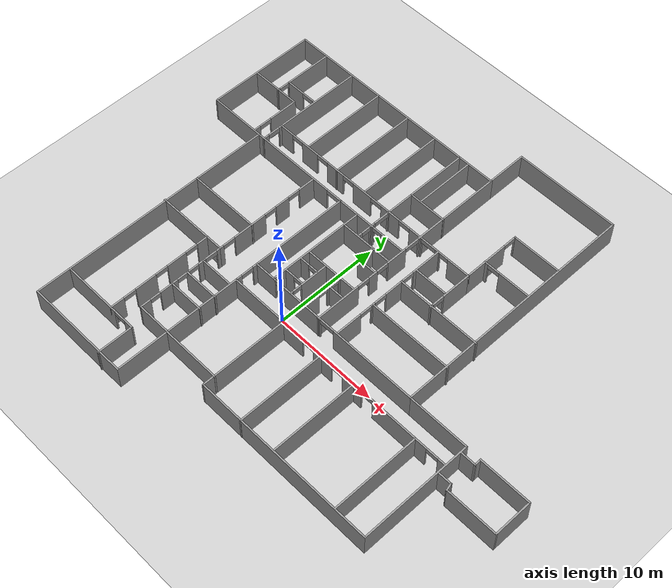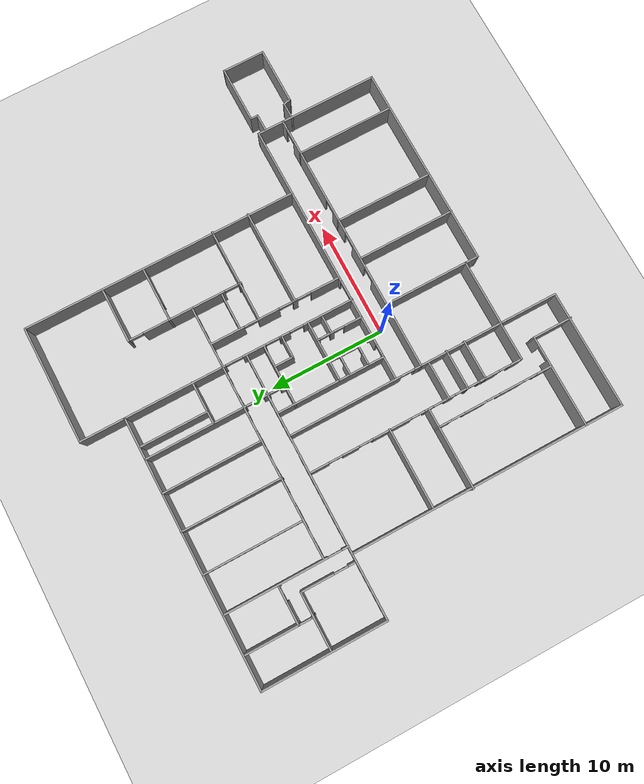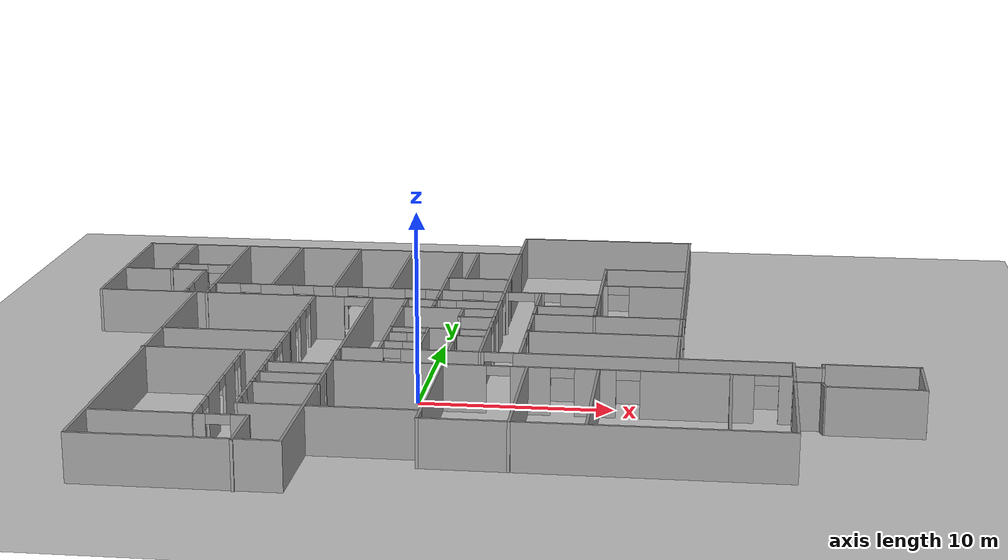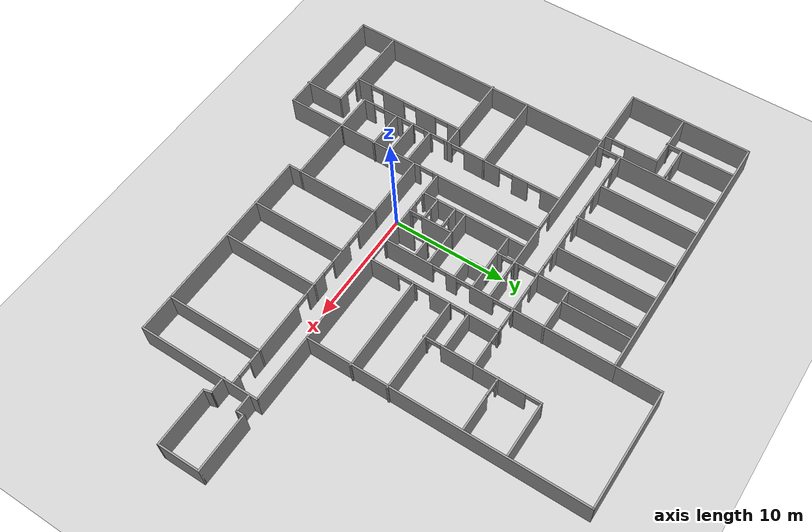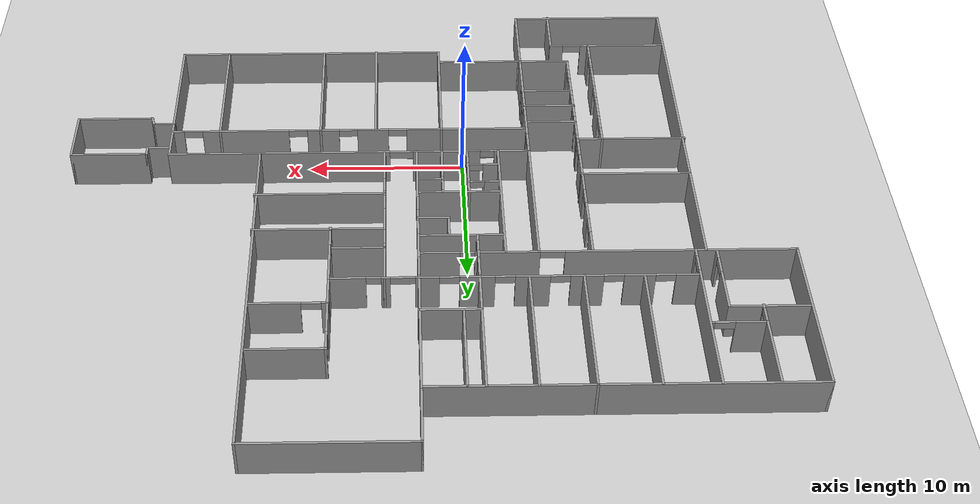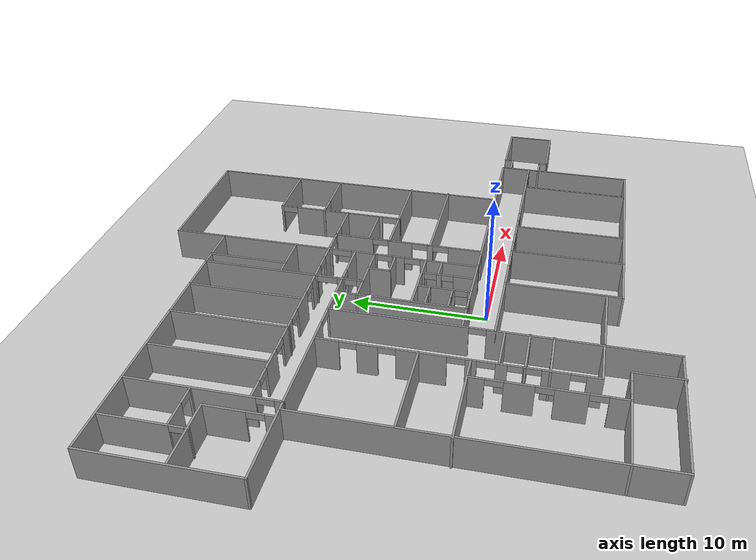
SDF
<sdf version="1.6">
 <world name="default">
  <light name="sun" type="directional">
   <pose>0 0 10 0 -0 0</pose>
   <diffuse>0.8 0.8 0.8 1</diffuse>
   <specular>0.2 0.2 0.2 1</specular>
   <attenuation>
    <range>1000</range>
    <constant>0.9</constant>
    <linear>0.01</linear>
    <quadratic>0.001</quadratic>
   </attenuation>
   <direction>-0.5 0.1 -0.9</direction>
  </light>
  <model name="ground_plane">
   <static>1</static>
   <link name="link">
    <collision name="collision">
     <geometry><plane><normal>0 0 1</normal><size>100 100</size></plane></geometry>
     <surface><friction><ode><mu>100</mu><mu2>50</mu2></ode></friction></surface>
    </collision>
    <visual name="visual">
     <cast_shadows>0</cast_shadows>
     <geometry><plane><normal>0 0 1</normal><size>100 100</size></plane></geometry>
     <material>
      <script><uri>file://media/materials/scripts/gazebo.material</uri><name>Gazebo/Grey</name></script>
     </material>
    </visual>
   </link>
  </model>
  <gravity>0 0 -9.8</gravity>
  <magnetic_field>6e-06 2.3e-05 -4.2e-05</magnetic_field>
  <atmosphere type="adiabatic"/>
  <physics name="default_physics" default="0" type="ode">
   <max_step_size>0.001</max_step_size>
   <real_time_factor>1</real_time_factor>
   <real_time_update_rate>1000</real_time_update_rate>
  </physics>
  <scene><ambient>0.4 0.4 0.4 1</ambient><background>0.7 0.7 0.7 1</background><shadows>1</shadows></scene>
  <spherical_coordinates>
   <surface_model>EARTH_WGS84</surface_model>
   <latitude_deg>0</latitude_deg>
   <longitude_deg>0</longitude_deg>
   <elevation>0</elevation>
   <heading_deg>0</heading_deg>
  </spherical_coordinates>
  <model name="ed21">
   <pose>2.72337 5.84388 0 0 -0 0</pose>
   <link name="Wall_10">
    <pose>1.71748 -4.65158 0 0 -0 3.14159</pose>
    <visual name="Wall_10_Visual_0">
     <pose>-4.52425 0 1.25 0 -0 0</pose>
     <geometry><box><size>8.4515 0.15 2.5</size></box></geometry>
     <material>
      <script><uri>file://media/materials/scripts/gazebo.material</uri><name>Gazebo/Grey</name></script>
      <ambient>1 1 1 1</ambient>
     </material>
     <meta><layer>0</layer></meta>
    </visual>
    <collision name="Wall_10_Collision_0">
     <geometry><box><size>8.4515 0.15 2.5</size></box></geometry>
     <pose>-4.52425 0 1.25 0 -0 0</pose>
    </collision>
    <visual name="Wall_10_Visual_1">
     <pose>3.36672 0 1.25 0 -0 0</pose>
     <geometry><box><size>4.33043 0.15 2.5</size></box></geometry>
     <material>
      <script><uri>file://media/materials/scripts/gazebo.material</uri><name>Gazebo/Grey</name></script>
      <ambient>1 1 1 1</ambient>
     </material>
     <meta><layer>0</layer></meta>
    </visual>
    <collision name="Wall_10_Collision_1">
     <geometry><box><size>4.33043 0.15 2.5</size></box></geometry>
     <pose>3.36672 0 1.25 0 -0 0</pose>
    </collision>
    <visual name="Wall_10_Visual_2">
     <pose>7.59097 0 1.25 0 -0 0</pose>
     <geometry><box><size>2.31806 0.15 2.5</size></box></geometry>
     <material>
      <script><uri>file://media/materials/scripts/gazebo.material</uri><name>Gazebo/Grey</name></script>
      <ambient>1 1 1 1</ambient>
     </material>
     <meta><layer>0</layer></meta>
    </visual>
    <collision name="Wall_10_Collision_2">
     <geometry><box><size>2.31806 0.15 2.5</size></box></geometry>
     <pose>7.59097 0 1.25 0 -0 0</pose>
    </collision>
    <visual name="Wall_10_Visual_3">
     <pose>0.451502 0 2.25 0 -0 0</pose>
     <geometry><box><size>1.5 0.15 0.5</size></box></geometry>
     <material>
      <script><uri>file://media/materials/scripts/gazebo.material</uri><name>Gazebo/Grey</name></script>
      <ambient>1 1 1 1</ambient>
     </material>
     <meta><layer>0</layer></meta>
    </visual>
    <collision name="Wall_10_Collision_3">
     <geometry><box><size>1.5 0.15 0.5</size></box></geometry>
     <pose>0.451502 0 2.25 0 -0 0</pose>
    </collision>
    <visual name="Wall_10_Visual_4">
     <pose>5.98194 0 2.25 0 -0 0</pose>
     <geometry><box><size>0.9 0.15 0.5</size></box></geometry>
     <material>
      <script><uri>file://media/materials/scripts/gazebo.material</uri><name>Gazebo/Grey</name></script>
      <ambient>1 1 1 1</ambient>
     </material>
     <meta><layer>0</layer></meta>
    </visual>
    <collision name="Wall_10_Collision_4">
     <geometry><box><size>0.9 0.15 0.5</size></box></geometry>
     <pose>5.98194 0 2.25 0 -0 0</pose>
    </collision>
   </link>
   <link name="Wall_101">
    <collision name="Wall_101_Collision">
     <geometry><box><size>5.25 0.15 2.5</size></box></geometry>
     <pose>0 0 1.25 0 -0 0</pose>
    </collision>
    <visual name="Wall_101_Visual">
     <pose>0 0 1.25 0 -0 0</pose>
     <geometry><box><size>5.25 0.15 2.5</size></box></geometry>
     <material>
      <script><uri>file://media/materials/scripts/gazebo.material</uri><name>Gazebo/Grey</name></script>
      <ambient>1 1 1 1</ambient>
     </material>
     <meta><layer>0</layer></meta>
    </visual>
    <pose>-2.36942 -0.737011 0 0 -0 0</pose>
   </link>
   <link name="Wall_103">
    <pose>-1.31646 -2.66201 0 0 0 -1.5708</pose>
    <visual name="Wall_103_Visual_0">
     <pose>-1.85926 0 1.25 0 -0 0</pose>
     <geometry><box><size>0.281471 0.15 2.5</size></box></geometry>
     <material>
      <script><uri>file://media/materials/scripts/gazebo.material</uri><name>Gazebo/Grey</name></script>
      <ambient>1 1 1 1</ambient>
     </material>
     <meta><layer>0</layer></meta>
    </visual>
    <collision name="Wall_103_Collision_0">
     <geometry><box><size>0.281471 0.15 2.5</size></box></geometry>
     <pose>-1.85926 0 1.25 0 -0 0</pose>
    </collision>
    <visual name="Wall_103_Visual_1">
     <pose>-0.633747 0 1.25 0 -0 0</pose>
     <geometry><box><size>0.369565 0.15 2.5</size></box></geometry>
     <material>
      <script><uri>file://media/materials/scripts/gazebo.material</uri><name>Gazebo/Grey</name></script>
      <ambient>1 1 1 1</ambient>
     </material>
     <meta><layer>0</layer></meta>
    </visual>
    <collision name="Wall_103_Collision_1">
     <geometry><box><size>0.369565 0.15 2.5</size></box></geometry>
     <pose>-0.633747 0 1.25 0 -0 0</pose>
    </collision>
    <visual name="Wall_103_Visual_2">
     <pose>1.22552 0 1.25 0 -0 0</pose>
     <geometry><box><size>1.54896 0.15 2.5</size></box></geometry>
     <material>
      <script><uri>file://media/materials/scripts/gazebo.material</uri><name>Gazebo/Grey</name></script>
      <ambient>1 1 1 1</ambient>
     </material>
     <meta><layer>0</layer></meta>
    </visual>
    <collision name="Wall_103_Collision_2">
     <geometry><box><size>1.54896 0.15 2.5</size></box></geometry>
     <pose>1.22552 0 1.25 0 -0 0</pose>
    </collision>
    <visual name="Wall_103_Visual_3">
     <pose>-1.26853 0 2.25 0 -0 0</pose>
     <geometry><box><size>0.9 0.15 0.5</size></box></geometry>
     <material>
      <script><uri>file://media/materials/scripts/gazebo.material</uri><name>Gazebo/Grey</name></script>
      <ambient>1 1 1 1</ambient>
     </material>
     <meta><layer>0</layer></meta>
    </visual>
    <collision name="Wall_103_Collision_3">
     <geometry><box><size>0.9 0.15 0.5</size></box></geometry>
     <pose>-1.26853 0 2.25 0 -0 0</pose>
    </collision>
    <visual name="Wall_103_Visual_4">
     <pose>0.001036 0 2.25 0 -0 0</pose>
     <geometry><box><size>0.9 0.15 0.5</size></box></geometry>
     <material>
      <script><uri>file://media/materials/scripts/gazebo.material</uri><name>Gazebo/Grey</name></script>
      <ambient>1 1 1 1</ambient>
     </material>
     <meta><layer>0</layer></meta>
    </visual>
    <collision name="Wall_103_Collision_4">
     <geometry><box><size>0.9 0.15 0.5</size></box></geometry>
     <pose>0.001036 0 2.25 0 -0 0</pose>
    </collision>
   </link>
   <link name="Wall_105">
    <collision name="Wall_105_Collision">
     <geometry><box><size>1.5 0.15 2.5</size></box></geometry>
     <pose>0 0 1.25 0 -0 0</pose>
    </collision>
    <visual name="Wall_105_Visual">
     <pose>0 0 1.25 0 -0 0</pose>
     <geometry><box><size>1.5 0.15 2.5</size></box></geometry>
     <material>
      <script><uri>file://media/materials/scripts/gazebo.material</uri><name>Gazebo/Grey</name></script>
      <ambient>1 1 1 1</ambient>
     </material>
     <meta><layer>0</layer></meta>
    </visual>
    <pose>-0.536524 -1.96132 0 0 -0 0</pose>
   </link>
   <link name="Wall_107">
    <pose>-2.96053 -2.66201 0 0 0 -1.5708</pose>
    <visual name="Wall_107_Visual_0">
     <pose>-0.577397 0 1.25 0 -0 0</pose>
     <geometry><box><size>2.84521 0.15 2.5</size></box></geometry>
     <material>
      <script><uri>file://media/materials/scripts/gazebo.material</uri><name>Gazebo/Grey</name></script>
      <ambient>1 1 1 1</ambient>
     </material>
     <meta><layer>0</layer></meta>
    </visual>
    <collision name="Wall_107_Collision_0">
     <geometry><box><size>2.84521 0.15 2.5</size></box></geometry>
     <pose>-0.577397 0 1.25 0 -0 0</pose>
    </collision>
    <visual name="Wall_107_Visual_1">
     <pose>1.8726 0 1.25 0 -0 0</pose>
     <geometry><box><size>0.254794 0.15 2.5</size></box></geometry>
     <material>
      <script><uri>file://media/materials/scripts/gazebo.material</uri><name>Gazebo/Grey</name></script>
      <ambient>1 1 1 1</ambient>
     </material>
     <meta><layer>0</layer></meta>
    </visual>
    <collision name="Wall_107_Collision_1">
     <geometry><box><size>0.254794 0.15 2.5</size></box></geometry>
     <pose>1.8726 0 1.25 0 -0 0</pose>
    </collision>
    <visual name="Wall_107_Visual_2">
     <pose>1.29521 0 2.25 0 -0 0</pose>
     <geometry><box><size>0.9 0.15 0.5</size></box></geometry>
     <material>
      <script><uri>file://media/materials/scripts/gazebo.material</uri><name>Gazebo/Grey</name></script>
      <ambient>1 1 1 1</ambient>
     </material>
     <meta><layer>0</layer></meta>
    </visual>
    <collision name="Wall_107_Collision_2">
     <geometry><box><size>0.9 0.15 0.5</size></box></geometry>
     <pose>1.29521 0 2.25 0 -0 0</pose>
    </collision>
   </link>
   <link name="Wall_109">
    <pose>-3.95944 -3.32554 0 0 -0 0</pose>
    <visual name="Wall_109_Visual_0">
     <pose>-0.486206 0 1.25 0 -0 0</pose>
     <geometry><box><size>1.02759 0.15 2.5</size></box></geometry>
     <material>
      <script><uri>file://media/materials/scripts/gazebo.material</uri><name>Gazebo/Grey</name></script>
      <ambient>1 1 1 1</ambient>
     </material>
     <meta><layer>0</layer></meta>
    </visual>
    <collision name="Wall_109_Collision_0">
     <geometry><box><size>1.02759 0.15 2.5</size></box></geometry>
     <pose>-0.486206 0 1.25 0 -0 0</pose>
    </collision>
    <visual name="Wall_109_Visual_1">
     <pose>0.963794 0 1.25 0 -0 0</pose>
     <geometry><box><size>0.072411 0.15 2.5</size></box></geometry>
     <material>
      <script><uri>file://media/materials/scripts/gazebo.material</uri><name>Gazebo/Grey</name></script>
      <ambient>1 1 1 1</ambient>
     </material>
     <meta><layer>0</layer></meta>
    </visual>
    <collision name="Wall_109_Collision_1">
     <geometry><box><size>0.072411 0.15 2.5</size></box></geometry>
     <pose>0.963794 0 1.25 0 -0 0</pose>
    </collision>
    <visual name="Wall_109_Visual_2">
     <pose>0.477589 0 2.25 0 -0 0</pose>
     <geometry><box><size>0.9 0.15 0.5</size></box></geometry>
     <material>
      <script><uri>file://media/materials/scripts/gazebo.material</uri><name>Gazebo/Grey</name></script>
      <ambient>1 1 1 1</ambient>
     </material>
     <meta><layer>0</layer></meta>
    </visual>
    <collision name="Wall_109_Collision_2">
     <geometry><box><size>0.9 0.15 0.5</size></box></geometry>
     <pose>0.477589 0 2.25 0 -0 0</pose>
    </collision>
   </link>
   <link name="Wall_111">
    <pose>-3.95944 -1.68148 0 0 -0 0</pose>
    <visual name="Wall_111_Visual_0">
     <pose>-0.494901 0 1.25 0 -0 0</pose>
     <geometry><box><size>1.0102 0.15 2.5</size></box></geometry>
     <material>
      <script><uri>file://media/materials/scripts/gazebo.material</uri><name>Gazebo/Grey</name></script>
      <ambient>1 1 1 1</ambient>
     </material>
     <meta><layer>0</layer></meta>
    </visual>
    <collision name="Wall_111_Collision_0">
     <geometry><box><size>1.0102 0.15 2.5</size></box></geometry>
     <pose>-0.494901 0 1.25 0 -0 0</pose>
    </collision>
    <visual name="Wall_111_Visual_1">
     <pose>0.955099 0 1.25 0 -0 0</pose>
     <geometry><box><size>0.089803 0.15 2.5</size></box></geometry>
     <material>
      <script><uri>file://media/materials/scripts/gazebo.material</uri><name>Gazebo/Grey</name></script>
      <ambient>1 1 1 1</ambient>
     </material>
     <meta><layer>0</layer></meta>
    </visual>
    <collision name="Wall_111_Collision_1">
     <geometry><box><size>0.089803 0.15 2.5</size></box></geometry>
     <pose>0.955099 0 1.25 0 -0 0</pose>
    </collision>
    <visual name="Wall_111_Visual_2">
     <pose>0.460197 0 2.25 0 -0 0</pose>
     <geometry><box><size>0.9 0.15 0.5</size></box></geometry>
     <material>
      <script><uri>file://media/materials/scripts/gazebo.material</uri><name>Gazebo/Grey</name></script>
      <ambient>1 1 1 1</ambient>
     </material>
     <meta><layer>0</layer></meta>
    </visual>
    <collision name="Wall_111_Collision_2">
     <geometry><box><size>0.9 0.15 0.5</size></box></geometry>
     <pose>0.460197 0 2.25 0 -0 0</pose>
    </collision>
   </link>
   <link name="Wall_113">
    <collision name="Wall_113_Collision">
     <geometry><box><size>1.5 0.15 2.5</size></box></geometry>
     <pose>0 0 1.25 0 -0 0</pose>
    </collision>
    <visual name="Wall_113_Visual">
     <pose>0 0 1.25 0 -0 0</pose>
     <geometry><box><size>1.5 0.15 2.5</size></box></geometry>
     <material>
      <script><uri>file://media/materials/scripts/gazebo.material</uri><name>Gazebo/Grey</name></script>
      <ambient>1 1 1 1</ambient>
     </material>
     <meta><layer>0</layer></meta>
    </visual>
    <pose>17.0325 -5.30032 0 0 -0 0</pose>
   </link>
   <link name="Wall_114">
    <collision name="Wall_114_Collision">
     <geometry><box><size>0.75 0.15 2.5</size></box></geometry>
     <pose>0 0 1.25 0 -0 0</pose>
    </collision>
    <visual name="Wall_114_Visual">
     <pose>0 0 1.25 0 -0 0</pose>
     <geometry><box><size>0.75 0.15 2.5</size></box></geometry>
     <material>
      <script><uri>file://media/materials/scripts/gazebo.material</uri><name>Gazebo/Grey</name></script>
      <ambient>1 1 1 1</ambient>
     </material>
     <meta><layer>0</layer></meta>
    </visual>
    <pose>17.7075 -5.00033 0 0 -0 1.5708</pose>
   </link>
   <link name="Wall_115">
    <collision name="Wall_115_Collision">
     <geometry><box><size>5 0.15 2.5</size></box></geometry>
     <pose>0 0 1.25 0 -0 0</pose>
    </collision>
    <visual name="Wall_115_Visual">
     <pose>0 0 1.25 0 -0 0</pose>
     <geometry><box><size>5 0.15 2.5</size></box></geometry>
     <material>
      <script><uri>file://media/materials/scripts/gazebo.material</uri><name>Gazebo/Grey</name></script>
      <ambient>1 1 1 1</ambient>
     </material>
     <meta><layer>0</layer></meta>
    </visual>
    <pose>20.1325 -4.70033 0 0 -0 0</pose>
   </link>
   <link name="Wall_116">
    <collision name="Wall_116_Collision">
     <geometry><box><size>3.75 0.15 2.5</size></box></geometry>
     <pose>0 0 1.25 0 -0 0</pose>
    </collision>
    <visual name="Wall_116_Visual">
     <pose>0 0 1.25 0 -0 0</pose>
     <geometry><box><size>3.75 0.15 2.5</size></box></geometry>
     <material>
      <script><uri>file://media/materials/scripts/gazebo.material</uri><name>Gazebo/Grey</name></script>
      <ambient>1 1 1 1</ambient>
     </material>
     <meta><layer>0</layer></meta>
    </visual>
    <pose>22.5575 -6.50033 0 0 0 -1.5708</pose>
   </link>
   <link name="Wall_12">
    <collision name="Wall_12_Collision">
     <geometry><box><size>6 0.15 2.5</size></box></geometry>
     <pose>0 0 1.25 0 -0 0</pose>
    </collision>
    <visual name="Wall_12_Visual">
     <pose>0 0 1.25 0 -0 0</pose>
     <geometry><box><size>6 0.15 2.5</size></box></geometry>
     <material>
      <script><uri>file://media/materials/scripts/gazebo.material</uri><name>Gazebo/Grey</name></script>
      <ambient>1 1 1 1</ambient>
     </material>
     <meta><layer>0</layer></meta>
    </visual>
    <pose>13.3175 -4.65158 0 0 -0 0</pose>
   </link>
   <link name="Wall_120">
    <collision name="Wall_120_Collision">
     <geometry><box><size>5 0.15 2.5</size></box></geometry>
     <pose>0 0 1.25 0 -0 0</pose>
    </collision>
    <visual name="Wall_120_Visual">
     <pose>0 0 1.25 0 -0 0</pose>
     <geometry><box><size>5 0.15 2.5</size></box></geometry>
     <material>
      <script><uri>file://media/materials/scripts/gazebo.material</uri><name>Gazebo/Grey</name></script>
      <ambient>1 1 1 1</ambient>
     </material>
     <meta><layer>0</layer></meta>
    </visual>
    <pose>20.1325 -8.30033 0 0 -0 3.14159</pose>
   </link>
   <link name="Wall_121">
    <collision name="Wall_121_Collision">
     <geometry><box><size>0.75 0.15 2.5</size></box></geometry>
     <pose>0 0 1.25 0 -0 0</pose>
    </collision>
    <visual name="Wall_121_Visual">
     <pose>0 0 1.25 0 -0 0</pose>
     <geometry><box><size>0.75 0.15 2.5</size></box></geometry>
     <material>
      <script><uri>file://media/materials/scripts/gazebo.material</uri><name>Gazebo/Grey</name></script>
      <ambient>1 1 1 1</ambient>
     </material>
     <meta><layer>0</layer></meta>
    </visual>
    <pose>17.6299 -8.01055 0 0 -0 1.8326</pose>
   </link>
   <link name="Wall_122">
    <collision name="Wall_122_Collision">
     <geometry><box><size>1.5 0.15 2.5</size></box></geometry>
     <pose>0 0 1.25 0 -0 0</pose>
    </collision>
    <visual name="Wall_122_Visual">
     <pose>0 0 1.25 0 -0 0</pose>
     <geometry><box><size>1.5 0.15 2.5</size></box></geometry>
     <material>
      <script><uri>file://media/materials/scripts/gazebo.material</uri><name>Gazebo/Grey</name></script>
      <ambient>1 1 1 1</ambient>
     </material>
     <meta><layer>0</layer></meta>
    </visual>
    <pose>16.8772 -7.72077 0 0 -0 3.14159</pose>
   </link>
   <link name="Wall_13">
    <collision name="Wall_13_Collision">
     <geometry><box><size>10.75 0.15 2.5</size></box></geometry>
     <pose>0 0 1.25 0 -0 0</pose>
    </collision>
    <visual name="Wall_13_Visual">
     <pose>0 0 1.25 0 -0 0</pose>
     <geometry><box><size>10.75 0.15 2.5</size></box></geometry>
     <material>
      <script><uri>file://media/materials/scripts/gazebo.material</uri><name>Gazebo/Grey</name></script>
      <ambient>1 1 1 1</ambient>
     </material>
     <meta><layer>0</layer></meta>
    </visual>
    <pose>16.2425 -9.95158 0 0 0 -1.5708</pose>
   </link>
   <link name="Wall_14">
    <collision name="Wall_14_Collision">
     <geometry><box><size>17.75 0.15 2.5</size></box></geometry>
     <pose>0 0 1.25 0 -0 0</pose>
    </collision>
    <visual name="Wall_14_Visual">
     <pose>0 0 1.25 0 -0 0</pose>
     <geometry><box><size>17.75 0.15 2.5</size></box></geometry>
     <material>
      <script><uri>file://media/materials/scripts/gazebo.material</uri><name>Gazebo/Grey</name></script>
      <ambient>1 1 1 1</ambient>
     </material>
     <meta><layer>0</layer></meta>
    </visual>
    <pose>7.44248 -15.2516 0 0 -0 3.14159</pose>
   </link>
   <link name="Wall_15">
    <collision name="Wall_15_Collision">
     <geometry><box><size>8.50066 0.15 2.5</size></box></geometry>
     <pose>0 0 1.25 0 -0 0</pose>
    </collision>
    <visual name="Wall_15_Visual">
     <pose>0 0 1.25 0 -0 0</pose>
     <geometry><box><size>8.50066 0.15 2.5</size></box></geometry>
     <material>
      <script><uri>file://media/materials/scripts/gazebo.material</uri><name>Gazebo/Grey</name></script>
      <ambient>1 1 1 1</ambient>
     </material>
     <meta><layer>0</layer></meta>
    </visual>
    <pose>-1.35752 -11.0766 0 0 -0 1.5708</pose>
   </link>
   <link name="Wall_16">
    <pose>7.44248 -6.90158 0 0 -0 0</pose>
    <visual name="Wall_16_Visual_0">
     <pose>-7.70401 0 1.25 0 -0 0</pose>
     <geometry><box><size>2.34198 0.15 2.5</size></box></geometry>
     <material>
      <script><uri>file://media/materials/scripts/gazebo.material</uri><name>Gazebo/Grey</name></script>
      <ambient>1 1 1 1</ambient>
     </material>
     <meta><layer>0</layer></meta>
    </visual>
    <collision name="Wall_16_Collision_0">
     <geometry><box><size>2.34198 0.15 2.5</size></box></geometry>
     <pose>-7.70401 0 1.25 0 -0 0</pose>
    </collision>
    <visual name="Wall_16_Visual_1">
     <pose>-4.31563 0 1.25 0 -0 0</pose>
     <geometry><box><size>2.03478 0.15 2.5</size></box></geometry>
     <material>
      <script><uri>file://media/materials/scripts/gazebo.material</uri><name>Gazebo/Grey</name></script>
      <ambient>1 1 1 1</ambient>
     </material>
     <meta><layer>0</layer></meta>
    </visual>
    <collision name="Wall_16_Collision_1">
     <geometry><box><size>2.03478 0.15 2.5</size></box></geometry>
     <pose>-4.31563 0 1.25 0 -0 0</pose>
    </collision>
    <visual name="Wall_16_Visual_2">
     <pose>-1.05511 0 1.25 0 -0 0</pose>
     <geometry><box><size>2.08626 0.15 2.5</size></box></geometry>
     <material>
      <script><uri>file://media/materials/scripts/gazebo.material</uri><name>Gazebo/Grey</name></script>
      <ambient>1 1 1 1</ambient>
     </material>
     <meta><layer>0</layer></meta>
    </visual>
    <collision name="Wall_16_Collision_2">
     <geometry><box><size>2.08626 0.15 2.5</size></box></geometry>
     <pose>-1.05511 0 1.25 0 -0 0</pose>
    </collision>
    <visual name="Wall_16_Visual_3">
     <pose>4.01135 0 1.25 0 -0 0</pose>
     <geometry><box><size>5.64666 0.15 2.5</size></box></geometry>
     <material>
      <script><uri>file://media/materials/scripts/gazebo.material</uri><name>Gazebo/Grey</name></script>
      <ambient>1 1 1 1</ambient>
     </material>
     <meta><layer>0</layer></meta>
    </visual>
    <collision name="Wall_16_Collision_3">
     <geometry><box><size>5.64666 0.15 2.5</size></box></geometry>
     <pose>4.01135 0 1.25 0 -0 0</pose>
    </collision>
    <visual name="Wall_16_Visual_4">
     <pose>8.45484 0 1.25 0 -0 0</pose>
     <geometry><box><size>0.840318 0.15 2.5</size></box></geometry>
     <material>
      <script><uri>file://media/materials/scripts/gazebo.material</uri><name>Gazebo/Grey</name></script>
      <ambient>1 1 1 1</ambient>
     </material>
     <meta><layer>0</layer></meta>
    </visual>
    <collision name="Wall_16_Collision_4">
     <geometry><box><size>0.840318 0.15 2.5</size></box></geometry>
     <pose>8.45484 0 1.25 0 -0 0</pose>
    </collision>
    <visual name="Wall_16_Visual_5">
     <pose>-5.93302 0 2.25 0 -0 0</pose>
     <geometry><box><size>1.2 0.15 0.5</size></box></geometry>
     <material>
      <script><uri>file://media/materials/scripts/gazebo.material</uri><name>Gazebo/Grey</name></script>
      <ambient>1 1 1 1</ambient>
     </material>
     <meta><layer>0</layer></meta>
    </visual>
    <collision name="Wall_16_Collision_5">
     <geometry><box><size>1.2 0.15 0.5</size></box></geometry>
     <pose>-5.93302 0 2.25 0 -0 0</pose>
    </collision>
    <visual name="Wall_16_Visual_6">
     <pose>-2.69824 0 2.25 0 -0 0</pose>
     <geometry><box><size>1.2 0.15 0.5</size></box></geometry>
     <material>
      <script><uri>file://media/materials/scripts/gazebo.material</uri><name>Gazebo/Grey</name></script>
      <ambient>1 1 1 1</ambient>
     </material>
     <meta><layer>0</layer></meta>
    </visual>
    <collision name="Wall_16_Collision_6">
     <geometry><box><size>1.2 0.15 0.5</size></box></geometry>
     <pose>-2.69824 0 2.25 0 -0 0</pose>
    </collision>
    <visual name="Wall_16_Visual_7">
     <pose>0.588022 0 2.25 0 -0 0</pose>
     <geometry><box><size>1.2 0.15 0.5</size></box></geometry>
     <material>
      <script><uri>file://media/materials/scripts/gazebo.material</uri><name>Gazebo/Grey</name></script>
      <ambient>1 1 1 1</ambient>
     </material>
     <meta><layer>0</layer></meta>
    </visual>
    <collision name="Wall_16_Collision_7">
     <geometry><box><size>1.2 0.15 0.5</size></box></geometry>
     <pose>0.588022 0 2.25 0 -0 0</pose>
    </collision>
    <visual name="Wall_16_Visual_8">
     <pose>7.43468 0 2.25 0 -0 0</pose>
     <geometry><box><size>1.2 0.15 0.5</size></box></geometry>
     <material>
      <script><uri>file://media/materials/scripts/gazebo.material</uri><name>Gazebo/Grey</name></script>
      <ambient>1 1 1 1</ambient>
     </material>
     <meta><layer>0</layer></meta>
    </visual>
    <collision name="Wall_16_Collision_8">
     <geometry><box><size>1.2 0.15 0.5</size></box></geometry>
     <pose>7.43468 0 2.25 0 -0 0</pose>
    </collision>
   </link>
   <link name="Wall_18">
    <collision name="Wall_18_Collision">
     <geometry><box><size>5.75 0.15 2.5</size></box></geometry>
     <pose>0 0 1.25 0 -0 0</pose>
    </collision>
    <visual name="Wall_18_Visual">
     <pose>0 0 1.25 0 -0 0</pose>
     <geometry><box><size>5.75 0.15 2.5</size></box></geometry>
     <material>
      <script><uri>file://media/materials/scripts/gazebo.material</uri><name>Gazebo/Grey</name></script>
      <ambient>1 1 1 1</ambient>
     </material>
     <meta><layer>0</layer></meta>
    </visual>
    <pose>-4.15144 -14.1344 0 0 -0 3.14159</pose>
   </link>
   <link name="Wall_2">
    <collision name="Wall_2_Collision">
     <geometry><box><size>10.25 0.15 2.5</size></box></geometry>
     <pose>0 0 1.25 0 -0 0</pose>
    </collision>
    <visual name="Wall_2_Visual">
     <pose>0 0 1.25 0 -0 0</pose>
     <geometry><box><size>10.25 0.15 2.5</size></box></geometry>
     <material>
      <script><uri>file://media/materials/scripts/gazebo.material</uri><name>Gazebo/Grey</name></script>
      <ambient>1 1 1 1</ambient>
     </material>
     <meta><layer>0</layer></meta>
    </visual>
    <pose>-12.0075 -19.1016 0 0 -0 0</pose>
   </link>
   <link name="Wall_23">
    <collision name="Wall_23_Collision">
     <geometry><box><size>5.75 0.15 2.5</size></box></geometry>
     <pose>0 0 1.25 0 -0 0</pose>
    </collision>
    <visual name="Wall_23_Visual">
     <pose>0 0 1.25 0 -0 0</pose>
     <geometry><box><size>5.75 0.15 2.5</size></box></geometry>
     <material>
      <script><uri>file://media/materials/scripts/gazebo.material</uri><name>Gazebo/Grey</name></script>
      <ambient>1 1 1 1</ambient>
     </material>
     <meta><layer>0</layer></meta>
    </visual>
    <pose>-4.15752 -6.90158 0 0 -0 3.14159</pose>
   </link>
   <link name="Wall_25">
    <collision name="Wall_25_Collision">
     <geometry><box><size>8.5 0.15 2.5</size></box></geometry>
     <pose>0 0 1.25 0 -0 0</pose>
    </collision>
    <visual name="Wall_25_Visual">
     <pose>0 0 1.25 0 -0 0</pose>
     <geometry><box><size>8.5 0.15 2.5</size></box></geometry>
     <material>
      <script><uri>file://media/materials/scripts/gazebo.material</uri><name>Gazebo/Grey</name></script>
      <ambient>1 1 1 1</ambient>
     </material>
     <meta><layer>0</layer></meta>
    </visual>
    <pose>2.95111 -11.1035 0 0 0 -1.5708</pose>
   </link>
   <link name="Wall_27">
    <collision name="Wall_27_Collision">
     <geometry><box><size>8.5 0.15 2.5</size></box></geometry>
     <pose>0 0 1.25 0 -0 0</pose>
    </collision>
    <visual name="Wall_27_Visual">
     <pose>0 0 1.25 0 -0 0</pose>
     <geometry><box><size>8.5 0.15 2.5</size></box></geometry>
     <material>
      <script><uri>file://media/materials/scripts/gazebo.material</uri><name>Gazebo/Grey</name></script>
      <ambient>1 1 1 1</ambient>
     </material>
     <meta><layer>0</layer></meta>
    </visual>
    <pose>6.55406 -11.0685 0 0 0 -1.5708</pose>
   </link>
   <link name="Wall_29">
    <collision name="Wall_29_Collision">
     <geometry><box><size>8.5 0.15 2.5</size></box></geometry>
     <pose>0 0 1.25 0 -0 0</pose>
    </collision>
    <visual name="Wall_29_Visual">
     <pose>0 0 1.25 0 -0 0</pose>
     <geometry><box><size>8.5 0.15 2.5</size></box></geometry>
     <material>
      <script><uri>file://media/materials/scripts/gazebo.material</uri><name>Gazebo/Grey</name></script>
      <ambient>1 1 1 1</ambient>
     </material>
     <meta><layer>0</layer></meta>
    </visual>
    <pose>13.1303 -11.0685 0 0 0 -1.5708</pose>
   </link>
   <link name="Wall_3">
    <pose>-6.95752 -7.17658 0 0 -0 1.5708</pose>
    <visual name="Wall_3_Visual_0">
     <pose>-5.57033 0 1.25 0 -0 0</pose>
     <geometry><box><size>12.8593 0.15 2.5</size></box></geometry>
     <material>
      <script><uri>file://media/materials/scripts/gazebo.material</uri><name>Gazebo/Grey</name></script>
      <ambient>1 1 1 1</ambient>
     </material>
     <meta><layer>0</layer></meta>
    </visual>
    <collision name="Wall_3_Collision_0">
     <geometry><box><size>12.8593 0.15 2.5</size></box></geometry>
     <pose>-5.57033 0 1.25 0 -0 0</pose>
    </collision>
    <visual name="Wall_3_Visual_1">
     <pose>7.02967 0 1.25 0 -0 0</pose>
     <geometry><box><size>9.94066 0.15 2.5</size></box></geometry>
     <material>
      <script><uri>file://media/materials/scripts/gazebo.material</uri><name>Gazebo/Grey</name></script>
      <ambient>1 1 1 1</ambient>
     </material>
     <meta><layer>0</layer></meta>
    </visual>
    <collision name="Wall_3_Collision_1">
     <geometry><box><size>9.94066 0.15 2.5</size></box></geometry>
     <pose>7.02967 0 1.25 0 -0 0</pose>
    </collision>
    <visual name="Wall_3_Visual_2">
     <pose>1.45934 0 2.25 0 -0 0</pose>
     <geometry><box><size>1.2 0.15 0.5</size></box></geometry>
     <material>
      <script><uri>file://media/materials/scripts/gazebo.material</uri><name>Gazebo/Grey</name></script>
      <ambient>1 1 1 1</ambient>
     </material>
     <meta><layer>0</layer></meta>
    </visual>
    <collision name="Wall_3_Collision_2">
     <geometry><box><size>1.2 0.15 0.5</size></box></geometry>
     <pose>1.45934 0 2.25 0 -0 0</pose>
    </collision>
   </link>
   <link name="Wall_31">
    <collision name="Wall_31_Collision">
     <geometry><box><size>24 0.15 2.5</size></box></geometry>
     <pose>0 0 1.25 0 -0 0</pose>
    </collision>
    <visual name="Wall_31_Visual">
     <pose>0 0 1.25 0 -0 0</pose>
     <geometry><box><size>24 0.15 2.5</size></box></geometry>
     <material>
      <script><uri>file://media/materials/scripts/gazebo.material</uri><name>Gazebo/Grey</name></script>
      <ambient>1 1 1 1</ambient>
     </material>
     <meta><layer>0</layer></meta>
    </visual>
    <pose>-17.0575 -7.17658 0 0 -0 1.5708</pose>
   </link>
   <link name="Wall_33">
    <pose>-13.1325 -15.8484 0 0 -0 0</pose>
    <visual name="Wall_33_Visual_0">
     <pose>-1.06245 0 1.25 0 -0 0</pose>
     <geometry><box><size>5.8751 0.15 2.5</size></box></geometry>
     <material>
      <script><uri>file://media/materials/scripts/gazebo.material</uri><name>Gazebo/Grey</name></script>
      <ambient>1 1 1 1</ambient>
     </material>
     <meta><layer>0</layer></meta>
    </visual>
    <collision name="Wall_33_Collision_0">
     <geometry><box><size>5.8751 0.15 2.5</size></box></geometry>
     <pose>-1.06245 0 1.25 0 -0 0</pose>
    </collision>
    <visual name="Wall_33_Visual_1">
     <pose>3.53755 0 1.25 0 -0 0</pose>
     <geometry><box><size>0.924895 0.15 2.5</size></box></geometry>
     <material>
      <script><uri>file://media/materials/scripts/gazebo.material</uri><name>Gazebo/Grey</name></script>
      <ambient>1 1 1 1</ambient>
     </material>
     <meta><layer>0</layer></meta>
    </visual>
    <collision name="Wall_33_Collision_1">
     <geometry><box><size>0.924895 0.15 2.5</size></box></geometry>
     <pose>3.53755 0 1.25 0 -0 0</pose>
    </collision>
    <visual name="Wall_33_Visual_2">
     <pose>2.47511 0 2.25 0 -0 0</pose>
     <geometry><box><size>1.2 0.15 0.5</size></box></geometry>
     <material>
      <script><uri>file://media/materials/scripts/gazebo.material</uri><name>Gazebo/Grey</name></script>
      <ambient>1 1 1 1</ambient>
     </material>
     <meta><layer>0</layer></meta>
    </visual>
    <collision name="Wall_33_Collision_2">
     <geometry><box><size>1.2 0.15 0.5</size></box></geometry>
     <pose>2.47511 0 2.25 0 -0 0</pose>
    </collision>
   </link>
   <link name="Wall_34">
    <collision name="Wall_34_Collision">
     <geometry><box><size>3.5 0.15 2.5</size></box></geometry>
     <pose>0 0 1.25 0 -0 0</pose>
    </collision>
    <visual name="Wall_34_Visual">
     <pose>0 0 1.25 0 -0 0</pose>
     <geometry><box><size>3.5 0.15 2.5</size></box></geometry>
     <material>
      <script><uri>file://media/materials/scripts/gazebo.material</uri><name>Gazebo/Grey</name></script>
      <ambient>1 1 1 1</ambient>
     </material>
     <meta><layer>0</layer></meta>
    </visual>
    <pose>-9.20752 -17.5234 0 0 0 -1.5708</pose>
   </link>
   <link name="Wall_36">
    <pose>-11.8105 -10.7984 0 0 -0 1.5708</pose>
    <visual name="Wall_36_Visual_0">
     <pose>-4.43495 0 1.25 0 -0 0</pose>
     <geometry><box><size>1.3801 0.15 2.5</size></box></geometry>
     <material>
      <script><uri>file://media/materials/scripts/gazebo.material</uri><name>Gazebo/Grey</name></script>
      <ambient>1 1 1 1</ambient>
     </material>
     <meta><layer>0</layer></meta>
    </visual>
    <collision name="Wall_36_Collision_0">
     <geometry><box><size>1.3801 0.15 2.5</size></box></geometry>
     <pose>-4.43495 0 1.25 0 -0 0</pose>
    </collision>
    <visual name="Wall_36_Visual_1">
     <pose>-1.48402 0 1.25 0 -0 0</pose>
     <geometry><box><size>2.12174 0.15 2.5</size></box></geometry>
     <material>
      <script><uri>file://media/materials/scripts/gazebo.material</uri><name>Gazebo/Grey</name></script>
      <ambient>1 1 1 1</ambient>
     </material>
     <meta><layer>0</layer></meta>
    </visual>
    <collision name="Wall_36_Collision_1">
     <geometry><box><size>2.12174 0.15 2.5</size></box></geometry>
     <pose>-1.48402 0 1.25 0 -0 0</pose>
    </collision>
    <visual name="Wall_36_Visual_2">
     <pose>1.75945 0 1.25 0 -0 0</pose>
     <geometry><box><size>1.96522 0.15 2.5</size></box></geometry>
     <material>
      <script><uri>file://media/materials/scripts/gazebo.material</uri><name>Gazebo/Grey</name></script>
      <ambient>1 1 1 1</ambient>
     </material>
     <meta><layer>0</layer></meta>
    </visual>
    <collision name="Wall_36_Collision_2">
     <geometry><box><size>1.96522 0.15 2.5</size></box></geometry>
     <pose>1.75945 0 1.25 0 -0 0</pose>
    </collision>
    <visual name="Wall_36_Visual_3">
     <pose>4.53353 0 1.25 0 -0 0</pose>
     <geometry><box><size>1.18294 0.15 2.5</size></box></geometry>
     <material>
      <script><uri>file://media/materials/scripts/gazebo.material</uri><name>Gazebo/Grey</name></script>
      <ambient>1 1 1 1</ambient>
     </material>
     <meta><layer>0</layer></meta>
    </visual>
    <collision name="Wall_36_Collision_3">
     <geometry><box><size>1.18294 0.15 2.5</size></box></geometry>
     <pose>4.53353 0 1.25 0 -0 0</pose>
    </collision>
    <visual name="Wall_36_Visual_4">
     <pose>-3.14489 0 2.25 0 -0 0</pose>
     <geometry><box><size>1.2 0.15 0.5</size></box></geometry>
     <material>
      <script><uri>file://media/materials/scripts/gazebo.material</uri><name>Gazebo/Grey</name></script>
      <ambient>1 1 1 1</ambient>
     </material>
     <meta><layer>0</layer></meta>
    </visual>
    <collision name="Wall_36_Collision_4">
     <geometry><box><size>1.2 0.15 0.5</size></box></geometry>
     <pose>-3.14489 0 2.25 0 -0 0</pose>
    </collision>
    <visual name="Wall_36_Visual_5">
     <pose>0.176845 0 2.25 0 -0 0</pose>
     <geometry><box><size>1.2 0.15 0.5</size></box></geometry>
     <material>
      <script><uri>file://media/materials/scripts/gazebo.material</uri><name>Gazebo/Grey</name></script>
      <ambient>1 1 1 1</ambient>
     </material>
     <meta><layer>0</layer></meta>
    </visual>
    <collision name="Wall_36_Collision_5">
     <geometry><box><size>1.2 0.15 0.5</size></box></geometry>
     <pose>0.176845 0 2.25 0 -0 0</pose>
    </collision>
    <visual name="Wall_36_Visual_6">
     <pose>3.34206 0 2.25 0 -0 0</pose>
     <geometry><box><size>1.2 0.15 0.5</size></box></geometry>
     <material>
      <script><uri>file://media/materials/scripts/gazebo.material</uri><name>Gazebo/Grey</name></script>
      <ambient>1 1 1 1</ambient>
     </material>
     <meta><layer>0</layer></meta>
    </visual>
    <collision name="Wall_36_Collision_6">
     <geometry><box><size>1.2 0.15 0.5</size></box></geometry>
     <pose>3.34206 0 2.25 0 -0 0</pose>
    </collision>
   </link>
   <link name="Wall_37">
    <collision name="Wall_37_Collision">
     <geometry><box><size>5.5 0.15 2.5</size></box></geometry>
     <pose>0 0 1.25 0 -0 0</pose>
    </collision>
    <visual name="Wall_37_Visual">
     <pose>0 0 1.25 0 -0 0</pose>
     <geometry><box><size>5.5 0.15 2.5</size></box></geometry>
     <material>
      <script><uri>file://media/materials/scripts/gazebo.material</uri><name>Gazebo/Grey</name></script>
      <ambient>1 1 1 1</ambient>
     </material>
     <meta><layer>0</layer></meta>
    </visual>
    <pose>-14.4855 -5.74843 0 0 -0 3.14159</pose>
   </link>
   <link name="Wall_39">
    <collision name="Wall_39_Collision">
     <geometry><box><size>1.75 0.15 2.5</size></box></geometry>
     <pose>0 0 1.25 0 -0 0</pose>
    </collision>
    <visual name="Wall_39_Visual">
     <pose>0 0 1.25 0 -0 0</pose>
     <geometry><box><size>1.75 0.15 2.5</size></box></geometry>
     <material>
      <script><uri>file://media/materials/scripts/gazebo.material</uri><name>Gazebo/Grey</name></script>
      <ambient>1 1 1 1</ambient>
     </material>
     <meta><layer>0</layer></meta>
    </visual>
    <pose>-11.0105 -5.74843 0 0 -0 0</pose>
   </link>
   <link name="Wall_4">
    <pose>-14.7575 4.74842 0 0 -0 3.14159</pose>
    <visual name="Wall_4_Visual_0">
     <pose>-7.79734 0 1.25 0 -0 0</pose>
     <geometry><box><size>0.15533 0.15 2.5</size></box></geometry>
     <material>
      <script><uri>file://media/materials/scripts/gazebo.material</uri><name>Gazebo/Grey</name></script>
      <ambient>1 1 1 1</ambient>
     </material>
     <meta><layer>0</layer></meta>
    </visual>
    <collision name="Wall_4_Collision_0">
     <geometry><box><size>0.15533 0.15 2.5</size></box></geometry>
     <pose>-7.79734 0 1.25 0 -0 0</pose>
    </collision>
    <visual name="Wall_4_Visual_1">
     <pose>0.827665 0 1.25 0 -0 0</pose>
     <geometry><box><size>14.0947 0.15 2.5</size></box></geometry>
     <material>
      <script><uri>file://media/materials/scripts/gazebo.material</uri><name>Gazebo/Grey</name></script>
      <ambient>1 1 1 1</ambient>
     </material>
     <meta><layer>0</layer></meta>
    </visual>
    <collision name="Wall_4_Collision_1">
     <geometry><box><size>14.0947 0.15 2.5</size></box></geometry>
     <pose>0.827665 0 1.25 0 -0 0</pose>
    </collision>
    <visual name="Wall_4_Visual_2">
     <pose>-6.96967 0 2.25 0 -0 0</pose>
     <geometry><box><size>1.5 0.15 0.5</size></box></geometry>
     <material>
      <script><uri>file://media/materials/scripts/gazebo.material</uri><name>Gazebo/Grey</name></script>
      <ambient>1 1 1 1</ambient>
     </material>
     <meta><layer>0</layer></meta>
    </visual>
    <collision name="Wall_4_Collision_2">
     <geometry><box><size>1.5 0.15 0.5</size></box></geometry>
     <pose>-6.96967 0 2.25 0 -0 0</pose>
    </collision>
   </link>
   <link name="Wall_40">
    <pose>-10.2105 -9.92343 0 0 0 -1.5708</pose>
    <visual name="Wall_40_Visual_0">
     <pose>-4.01505 0 1.25 0 -0 0</pose>
     <geometry><box><size>0.469895 0.15 2.5</size></box></geometry>
     <material>
      <script><uri>file://media/materials/scripts/gazebo.material</uri><name>Gazebo/Grey</name></script>
      <ambient>1 1 1 1</ambient>
     </material>
     <meta><layer>0</layer></meta>
    </visual>
    <collision name="Wall_40_Collision_0">
     <geometry><box><size>0.469895 0.15 2.5</size></box></geometry>
     <pose>-4.01505 0 1.25 0 -0 0</pose>
    </collision>
    <visual name="Wall_40_Visual_1">
     <pose>-2.19967 0 1.25 0 -0 0</pose>
     <geometry><box><size>0.760869 0.15 2.5</size></box></geometry>
     <material>
      <script><uri>file://media/materials/scripts/gazebo.material</uri><name>Gazebo/Grey</name></script>
      <ambient>1 1 1 1</ambient>
     </material>
     <meta><layer>0</layer></meta>
    </visual>
    <collision name="Wall_40_Collision_1">
     <geometry><box><size>0.760869 0.15 2.5</size></box></geometry>
     <pose>-2.19967 0 1.25 0 -0 0</pose>
    </collision>
    <visual name="Wall_40_Visual_2">
     <pose>-0.719236 0 1.25 0 -0 0</pose>
     <geometry><box><size>0.2 0.15 2.5</size></box></geometry>
     <material>
      <script><uri>file://media/materials/scripts/gazebo.material</uri><name>Gazebo/Grey</name></script>
      <ambient>1 1 1 1</ambient>
     </material>
     <meta><layer>0</layer></meta>
    </visual>
    <collision name="Wall_40_Collision_2">
     <geometry><box><size>0.2 0.15 2.5</size></box></geometry>
     <pose>-0.719236 0 1.25 0 -0 0</pose>
    </collision>
    <visual name="Wall_40_Visual_3">
     <pose>1.28076 0 1.25 0 -0 0</pose>
     <geometry><box><size>1.8 0.15 2.5</size></box></geometry>
     <material>
      <script><uri>file://media/materials/scripts/gazebo.material</uri><name>Gazebo/Grey</name></script>
      <ambient>1 1 1 1</ambient>
     </material>
     <meta><layer>0</layer></meta>
    </visual>
    <collision name="Wall_40_Collision_3">
     <geometry><box><size>1.8 0.15 2.5</size></box></geometry>
     <pose>1.28076 0 1.25 0 -0 0</pose>
    </collision>
    <visual name="Wall_40_Visual_4">
     <pose>3.71538 0 1.25 0 -0 0</pose>
     <geometry><box><size>1.06924 0.15 2.5</size></box></geometry>
     <material>
      <script><uri>file://media/materials/scripts/gazebo.material</uri><name>Gazebo/Grey</name></script>
      <ambient>1 1 1 1</ambient>
     </material>
     <meta><layer>0</layer></meta>
    </visual>
    <collision name="Wall_40_Collision_4">
     <geometry><box><size>1.06924 0.15 2.5</size></box></geometry>
     <pose>3.71538 0 1.25 0 -0 0</pose>
    </collision>
    <visual name="Wall_40_Visual_5">
     <pose>-3.18011 0 2.25 0 -0 0</pose>
     <geometry><box><size>1.2 0.15 0.5</size></box></geometry>
     <material>
      <script><uri>file://media/materials/scripts/gazebo.material</uri><name>Gazebo/Grey</name></script>
      <ambient>1 1 1 1</ambient>
     </material>
     <meta><layer>0</layer></meta>
    </visual>
    <collision name="Wall_40_Collision_5">
     <geometry><box><size>1.2 0.15 0.5</size></box></geometry>
     <pose>-3.18011 0 2.25 0 -0 0</pose>
    </collision>
    <visual name="Wall_40_Visual_6">
     <pose>-1.31924 0 2.25 0 -0 0</pose>
     <geometry><box><size>1 0.15 0.5</size></box></geometry>
     <material>
      <script><uri>file://media/materials/scripts/gazebo.material</uri><name>Gazebo/Grey</name></script>
      <ambient>1 1 1 1</ambient>
     </material>
     <meta><layer>0</layer></meta>
    </visual>
    <collision name="Wall_40_Collision_6">
     <geometry><box><size>1 0.15 0.5</size></box></geometry>
     <pose>-1.31924 0 2.25 0 -0 0</pose>
    </collision>
    <visual name="Wall_40_Visual_7">
     <pose>-0.119236 0 2.25 0 -0 0</pose>
     <geometry><box><size>1 0.15 0.5</size></box></geometry>
     <material>
      <script><uri>file://media/materials/scripts/gazebo.material</uri><name>Gazebo/Grey</name></script>
      <ambient>1 1 1 1</ambient>
     </material>
     <meta><layer>0</layer></meta>
    </visual>
    <collision name="Wall_40_Collision_7">
     <geometry><box><size>1 0.15 0.5</size></box></geometry>
     <pose>-0.119236 0 2.25 0 -0 0</pose>
    </collision>
    <visual name="Wall_40_Visual_8">
     <pose>2.68076 0 2.25 0 -0 0</pose>
     <geometry><box><size>1 0.15 0.5</size></box></geometry>
     <material>
      <script><uri>file://media/materials/scripts/gazebo.material</uri><name>Gazebo/Grey</name></script>
      <ambient>1 1 1 1</ambient>
     </material>
     <meta><layer>0</layer></meta>
    </visual>
    <collision name="Wall_40_Collision_8">
     <geometry><box><size>1 0.15 0.5</size></box></geometry>
     <pose>2.68076 0 2.25 0 -0 0</pose>
    </collision>
   </link>
   <link name="Wall_41">
    <collision name="Wall_41_Collision">
     <geometry><box><size>3.5 0.15 2.5</size></box></geometry>
     <pose>0 0 1.25 0 -0 0</pose>
    </collision>
    <visual name="Wall_41_Visual">
     <pose>0 0 1.25 0 -0 0</pose>
     <geometry><box><size>3.5 0.15 2.5</size></box></geometry>
     <material>
      <script><uri>file://media/materials/scripts/gazebo.material</uri><name>Gazebo/Grey</name></script>
      <ambient>1 1 1 1</ambient>
     </material>
     <meta><layer>0</layer></meta>
    </visual>
    <pose>-8.5355 -14.0984 0 0 -0 0</pose>
   </link>
   <link name="Wall_43">
    <collision name="Wall_43_Collision">
     <geometry><box><size>3.5 0.15 2.5</size></box></geometry>
     <pose>0 0 1.25 0 -0 0</pose>
    </collision>
    <visual name="Wall_43_Visual">
     <pose>0 0 1.25 0 -0 0</pose>
     <geometry><box><size>3.5 0.15 2.5</size></box></geometry>
     <material>
      <script><uri>file://media/materials/scripts/gazebo.material</uri><name>Gazebo/Grey</name></script>
      <ambient>1 1 1 1</ambient>
     </material>
     <meta><layer>0</layer></meta>
    </visual>
    <pose>-8.5614 -10.8463 0 0 -0 0</pose>
   </link>
   <link name="Wall_45">
    <collision name="Wall_45_Collision">
     <geometry><box><size>3.5 0.15 2.5</size></box></geometry>
     <pose>0 0 1.25 0 -0 0</pose>
    </collision>
    <visual name="Wall_45_Visual">
     <pose>0 0 1.25 0 -0 0</pose>
     <geometry><box><size>3.5 0.15 2.5</size></box></geometry>
     <material>
      <script><uri>file://media/materials/scripts/gazebo.material</uri><name>Gazebo/Grey</name></script>
      <ambient>1 1 1 1</ambient>
     </material>
     <meta><layer>0</layer></meta>
    </visual>
    <pose>-8.5614 -9.23718 0 0 -0 0</pose>
   </link>
   <link name="Wall_47">
    <collision name="Wall_47_Collision">
     <geometry><box><size>3.25 0.15 2.5</size></box></geometry>
     <pose>0 0 1.25 0 -0 0</pose>
    </collision>
    <visual name="Wall_47_Visual">
     <pose>0 0 1.25 0 -0 0</pose>
     <geometry><box><size>3.25 0.15 2.5</size></box></geometry>
     <material>
      <script><uri>file://media/materials/scripts/gazebo.material</uri><name>Gazebo/Grey</name></script>
      <ambient>1 1 1 1</ambient>
     </material>
     <meta><layer>0</layer></meta>
    </visual>
    <pose>-8.65142 -7.55814 0 0 -0 0</pose>
   </link>
   <link name="Wall_49">
    <pose>-10.2105 -0.573425 0 0 -0 1.5708</pose>
    <visual name="Wall_49_Visual_0">
     <pose>-5.03603 0 1.25 0 -0 0</pose>
     <geometry><box><size>0.427931 0.15 2.5</size></box></geometry>
     <material>
      <script><uri>file://media/materials/scripts/gazebo.material</uri><name>Gazebo/Grey</name></script>
      <ambient>1 1 1 1</ambient>
     </material>
     <meta><layer>0</layer></meta>
    </visual>
    <collision name="Wall_49_Collision_0">
     <geometry><box><size>0.427931 0.15 2.5</size></box></geometry>
     <pose>-5.03603 0 1.25 0 -0 0</pose>
    </collision>
    <visual name="Wall_49_Visual_1">
     <pose>-1.92642 0 1.25 0 -0 0</pose>
     <geometry><box><size>3.3913 0.15 2.5</size></box></geometry>
     <material>
      <script><uri>file://media/materials/scripts/gazebo.material</uri><name>Gazebo/Grey</name></script>
      <ambient>1 1 1 1</ambient>
     </material>
     <meta><layer>0</layer></meta>
    </visual>
    <collision name="Wall_49_Collision_1">
     <geometry><box><size>3.3913 0.15 2.5</size></box></geometry>
     <pose>-1.92642 0 1.25 0 -0 0</pose>
    </collision>
    <visual name="Wall_49_Visual_2">
     <pose>1.69097 0 1.25 0 -0 0</pose>
     <geometry><box><size>1.44348 0.15 2.5</size></box></geometry>
     <material>
      <script><uri>file://media/materials/scripts/gazebo.material</uri><name>Gazebo/Grey</name></script>
      <ambient>1 1 1 1</ambient>
     </material>
     <meta><layer>0</layer></meta>
    </visual>
    <collision name="Wall_49_Collision_2">
     <geometry><box><size>1.44348 0.15 2.5</size></box></geometry>
     <pose>1.69097 0 1.25 0 -0 0</pose>
    </collision>
    <visual name="Wall_49_Visual_3">
     <pose>4.43136 0 1.25 0 -0 0</pose>
     <geometry><box><size>1.63729 0.15 2.5</size></box></geometry>
     <material>
      <script><uri>file://media/materials/scripts/gazebo.material</uri><name>Gazebo/Grey</name></script>
      <ambient>1 1 1 1</ambient>
     </material>
     <meta><layer>0</layer></meta>
    </visual>
    <collision name="Wall_49_Collision_3">
     <geometry><box><size>1.63729 0.15 2.5</size></box></geometry>
     <pose>4.43136 0 1.25 0 -0 0</pose>
    </collision>
    <visual name="Wall_49_Visual_4">
     <pose>-4.22207 0 2.25 0 -0 0</pose>
     <geometry><box><size>1.2 0.15 0.5</size></box></geometry>
     <material>
      <script><uri>file://media/materials/scripts/gazebo.material</uri><name>Gazebo/Grey</name></script>
      <ambient>1 1 1 1</ambient>
     </material>
     <meta><layer>0</layer></meta>
    </visual>
    <collision name="Wall_49_Collision_4">
     <geometry><box><size>1.2 0.15 0.5</size></box></geometry>
     <pose>-4.22207 0 2.25 0 -0 0</pose>
    </collision>
    <visual name="Wall_49_Visual_5">
     <pose>0.369235 0 2.25 0 -0 0</pose>
     <geometry><box><size>1.2 0.15 0.5</size></box></geometry>
     <material>
      <script><uri>file://media/materials/scripts/gazebo.material</uri><name>Gazebo/Grey</name></script>
      <ambient>1 1 1 1</ambient>
     </material>
     <meta><layer>0</layer></meta>
    </visual>
    <collision name="Wall_49_Collision_5">
     <geometry><box><size>1.2 0.15 0.5</size></box></geometry>
     <pose>0.369235 0 2.25 0 -0 0</pose>
    </collision>
    <visual name="Wall_49_Visual_6">
     <pose>3.01271 0 2.25 0 -0 0</pose>
     <geometry><box><size>1.2 0.15 0.5</size></box></geometry>
     <material>
      <script><uri>file://media/materials/scripts/gazebo.material</uri><name>Gazebo/Grey</name></script>
      <ambient>1 1 1 1</ambient>
     </material>
     <meta><layer>0</layer></meta>
    </visual>
    <collision name="Wall_49_Collision_6">
     <geometry><box><size>1.2 0.15 0.5</size></box></geometry>
     <pose>3.01271 0 2.25 0 -0 0</pose>
    </collision>
   </link>
   <link name="Wall_5">
    <collision name="Wall_5_Collision">
     <geometry><box><size>10.75 0.15 2.5</size></box></geometry>
     <pose>0 0 1.25 0 -0 0</pose>
    </collision>
    <visual name="Wall_5_Visual">
     <pose>0 0 1.25 0 -0 0</pose>
     <geometry><box><size>10.75 0.15 2.5</size></box></geometry>
     <material>
      <script><uri>file://media/materials/scripts/gazebo.material</uri><name>Gazebo/Grey</name></script>
      <ambient>1 1 1 1</ambient>
     </material>
     <meta><layer>0</layer></meta>
    </visual>
    <pose>-22.5575 10.0484 0 0 -0 1.5708</pose>
   </link>
   <link name="Wall_51">
    <collision name="Wall_51_Collision">
     <geometry><box><size>7 0.15 2.5</size></box></geometry>
     <pose>0 0 1.25 0 -0 0</pose>
    </collision>
    <visual name="Wall_51_Visual">
     <pose>0 0 1.25 0 -0 0</pose>
     <geometry><box><size>7 0.15 2.5</size></box></geometry>
     <material>
      <script><uri>file://media/materials/scripts/gazebo.material</uri><name>Gazebo/Grey</name></script>
      <ambient>1 1 1 1</ambient>
     </material>
     <meta><layer>0</layer></meta>
    </visual>
    <pose>-13.5975 -2.31112 0 0 -0 0</pose>
   </link>
   <link name="Wall_53">
    <pose>-16.4279 10.0199 0 0 -0 1.5708</pose>
    <visual name="Wall_53_Visual_0">
     <pose>-5.05606 0 1.25 0 -0 0</pose>
     <geometry><box><size>0.637879 0.15 2.5</size></box></geometry>
     <material>
      <script><uri>file://media/materials/scripts/gazebo.material</uri><name>Gazebo/Grey</name></script>
      <ambient>1 1 1 1</ambient>
     </material>
     <meta><layer>0</layer></meta>
    </visual>
    <collision name="Wall_53_Collision_0">
     <geometry><box><size>0.637879 0.15 2.5</size></box></geometry>
     <pose>-5.05606 0 1.25 0 -0 0</pose>
    </collision>
    <visual name="Wall_53_Visual_1">
     <pose>0.918939 0 1.25 0 -0 0</pose>
     <geometry><box><size>8.91212 0.15 2.5</size></box></geometry>
     <material>
      <script><uri>file://media/materials/scripts/gazebo.material</uri><name>Gazebo/Grey</name></script>
      <ambient>1 1 1 1</ambient>
     </material>
     <meta><layer>0</layer></meta>
    </visual>
    <collision name="Wall_53_Collision_1">
     <geometry><box><size>8.91212 0.15 2.5</size></box></geometry>
     <pose>0.918939 0 1.25 0 -0 0</pose>
    </collision>
    <visual name="Wall_53_Visual_2">
     <pose>-4.13712 0 2.25 0 -0 0</pose>
     <geometry><box><size>1.2 0.15 0.5</size></box></geometry>
     <material>
      <script><uri>file://media/materials/scripts/gazebo.material</uri><name>Gazebo/Grey</name></script>
      <ambient>1 1 1 1</ambient>
     </material>
     <meta><layer>0</layer></meta>
    </visual>
    <collision name="Wall_53_Collision_2">
     <geometry><box><size>1.2 0.15 0.5</size></box></geometry>
     <pose>-4.13712 0 2.25 0 -0 0</pose>
    </collision>
   </link>
   <link name="Wall_55">
    <pose>-5.37788 6.8187 0 0 -0 0</pose>
    <visual name="Wall_55_Visual_0">
     <pose>-10.3544 0 1.25 0 -0 0</pose>
     <geometry><box><size>1.54112 0.15 2.5</size></box></geometry>
     <material>
      <script><uri>file://media/materials/scripts/gazebo.material</uri><name>Gazebo/Grey</name></script>
      <ambient>1 1 1 1</ambient>
     </material>
     <meta><layer>0</layer></meta>
    </visual>
    <collision name="Wall_55_Collision_0">
     <geometry><box><size>1.54112 0.15 2.5</size></box></geometry>
     <pose>-10.3544 0 1.25 0 -0 0</pose>
    </collision>
    <visual name="Wall_55_Visual_1">
     <pose>-7.44475 0 1.25 0 -0 0</pose>
     <geometry><box><size>1.87826 0.15 2.5</size></box></geometry>
     <material>
      <script><uri>file://media/materials/scripts/gazebo.material</uri><name>Gazebo/Grey</name></script>
      <ambient>1 1 1 1</ambient>
     </material>
     <meta><layer>0</layer></meta>
    </visual>
    <collision name="Wall_55_Collision_1">
     <geometry><box><size>1.87826 0.15 2.5</size></box></geometry>
     <pose>-7.44475 0 1.25 0 -0 0</pose>
    </collision>
    <visual name="Wall_55_Visual_2">
     <pose>-4.31432 0 1.25 0 -0 0</pose>
     <geometry><box><size>1.98261 0.15 2.5</size></box></geometry>
     <material>
      <script><uri>file://media/materials/scripts/gazebo.material</uri><name>Gazebo/Grey</name></script>
      <ambient>1 1 1 1</ambient>
     </material>
     <meta><layer>0</layer></meta>
    </visual>
    <collision name="Wall_55_Collision_2">
     <geometry><box><size>1.98261 0.15 2.5</size></box></geometry>
     <pose>-4.31432 0 1.25 0 -0 0</pose>
    </collision>
    <visual name="Wall_55_Visual_3">
     <pose>-1.07954 0 1.25 0 -0 0</pose>
     <geometry><box><size>2.08696 0.15 2.5</size></box></geometry>
     <material>
      <script><uri>file://media/materials/scripts/gazebo.material</uri><name>Gazebo/Grey</name></script>
      <ambient>1 1 1 1</ambient>
     </material>
     <meta><layer>0</layer></meta>
    </visual>
    <collision name="Wall_55_Collision_3">
     <geometry><box><size>2.08696 0.15 2.5</size></box></geometry>
     <pose>-1.07954 0 1.25 0 -0 0</pose>
    </collision>
    <visual name="Wall_55_Visual_4">
     <pose>2.21611 0 1.25 0 -0 0</pose>
     <geometry><box><size>2.10435 0.15 2.5</size></box></geometry>
     <material>
      <script><uri>file://media/materials/scripts/gazebo.material</uri><name>Gazebo/Grey</name></script>
      <ambient>1 1 1 1</ambient>
     </material>
     <meta><layer>0</layer></meta>
    </visual>
    <collision name="Wall_55_Collision_4">
     <geometry><box><size>2.10435 0.15 2.5</size></box></geometry>
     <pose>2.21611 0 1.25 0 -0 0</pose>
    </collision>
    <visual name="Wall_55_Visual_5">
     <pose>5.1759 0 1.25 0 -0 0</pose>
     <geometry><box><size>1.41522 0.15 2.5</size></box></geometry>
     <material>
      <script><uri>file://media/materials/scripts/gazebo.material</uri><name>Gazebo/Grey</name></script>
      <ambient>1 1 1 1</ambient>
     </material>
     <meta><layer>0</layer></meta>
    </visual>
    <collision name="Wall_55_Collision_5">
     <geometry><box><size>1.41522 0.15 2.5</size></box></geometry>
     <pose>5.1759 0 1.25 0 -0 0</pose>
    </collision>
    <visual name="Wall_55_Visual_6">
     <pose>7.65307 0 1.25 0 -0 0</pose>
     <geometry><box><size>0.53913 0.15 2.5</size></box></geometry>
     <material>
      <script><uri>file://media/materials/scripts/gazebo.material</uri><name>Gazebo/Grey</name></script>
      <ambient>1 1 1 1</ambient>
     </material>
     <meta><layer>0</layer></meta>
    </visual>
    <collision name="Wall_55_Collision_6">
     <geometry><box><size>0.53913 0.15 2.5</size></box></geometry>
     <pose>7.65307 0 1.25 0 -0 0</pose>
    </collision>
    <visual name="Wall_55_Visual_7">
     <pose>9.97382 0 1.25 0 -0 0</pose>
     <geometry><box><size>2.30236 0.15 2.5</size></box></geometry>
     <material>
      <script><uri>file://media/materials/scripts/gazebo.material</uri><name>Gazebo/Grey</name></script>
      <ambient>1 1 1 1</ambient>
     </material>
     <meta><layer>0</layer></meta>
    </visual>
    <collision name="Wall_55_Collision_7">
     <geometry><box><size>2.30236 0.15 2.5</size></box></geometry>
     <pose>9.97382 0 1.25 0 -0 0</pose>
    </collision>
    <visual name="Wall_55_Visual_8">
     <pose>-8.98389 0 2.25 0 -0 0</pose>
     <geometry><box><size>1.2 0.15 0.5</size></box></geometry>
     <material>
      <script><uri>file://media/materials/scripts/gazebo.material</uri><name>Gazebo/Grey</name></script>
      <ambient>1 1 1 1</ambient>
     </material>
     <meta><layer>0</layer></meta>
    </visual>
    <collision name="Wall_55_Collision_8">
     <geometry><box><size>1.2 0.15 0.5</size></box></geometry>
     <pose>-8.98389 0 2.25 0 -0 0</pose>
    </collision>
    <visual name="Wall_55_Visual_9">
     <pose>-5.90562 0 2.25 0 -0 0</pose>
     <geometry><box><size>1.2 0.15 0.5</size></box></geometry>
     <material>
      <script><uri>file://media/materials/scripts/gazebo.material</uri><name>Gazebo/Grey</name></script>
      <ambient>1 1 1 1</ambient>
     </material>
     <meta><layer>0</layer></meta>
    </visual>
    <collision name="Wall_55_Collision_9">
     <geometry><box><size>1.2 0.15 0.5</size></box></geometry>
     <pose>-5.90562 0 2.25 0 -0 0</pose>
    </collision>
    <visual name="Wall_55_Visual_10">
     <pose>-2.72302 0 2.25 0 -0 0</pose>
     <geometry><box><size>1.2 0.15 0.5</size></box></geometry>
     <material>
      <script><uri>file://media/materials/scripts/gazebo.material</uri><name>Gazebo/Grey</name></script>
      <ambient>1 1 1 1</ambient>
     </material>
     <meta><layer>0</layer></meta>
    </visual>
    <collision name="Wall_55_Collision_10">
     <geometry><box><size>1.2 0.15 0.5</size></box></geometry>
     <pose>-2.72302 0 2.25 0 -0 0</pose>
    </collision>
    <visual name="Wall_55_Visual_11">
     <pose>0.563941 0 2.25 0 -0 0</pose>
     <geometry><box><size>1.2 0.15 0.5</size></box></geometry>
     <material>
      <script><uri>file://media/materials/scripts/gazebo.material</uri><name>Gazebo/Grey</name></script>
      <ambient>1 1 1 1</ambient>
     </material>
     <meta><layer>0</layer></meta>
    </visual>
    <collision name="Wall_55_Collision_11">
     <geometry><box><size>1.2 0.15 0.5</size></box></geometry>
     <pose>0.563941 0 2.25 0 -0 0</pose>
    </collision>
    <visual name="Wall_55_Visual_12">
     <pose>3.86829 0 2.25 0 -0 0</pose>
     <geometry><box><size>1.2 0.15 0.5</size></box></geometry>
     <material>
      <script><uri>file://media/materials/scripts/gazebo.material</uri><name>Gazebo/Grey</name></script>
      <ambient>1 1 1 1</ambient>
     </material>
     <meta><layer>0</layer></meta>
    </visual>
    <collision name="Wall_55_Collision_12">
     <geometry><box><size>1.2 0.15 0.5</size></box></geometry>
     <pose>3.86829 0 2.25 0 -0 0</pose>
    </collision>
    <visual name="Wall_55_Visual_13">
     <pose>6.63351 0 2.25 0 -0 0</pose>
     <geometry><box><size>1.5 0.15 0.5</size></box></geometry>
     <material>
      <script><uri>file://media/materials/scripts/gazebo.material</uri><name>Gazebo/Grey</name></script>
      <ambient>1 1 1 1</ambient>
     </material>
     <meta><layer>0</layer></meta>
    </visual>
    <collision name="Wall_55_Collision_13">
     <geometry><box><size>1.5 0.15 0.5</size></box></geometry>
     <pose>6.63351 0 2.25 0 -0 0</pose>
    </collision>
    <visual name="Wall_55_Visual_14">
     <pose>8.37264 0 2.25 0 -0 0</pose>
     <geometry><box><size>0.9 0.15 0.5</size></box></geometry>
     <material>
      <script><uri>file://media/materials/scripts/gazebo.material</uri><name>Gazebo/Grey</name></script>
      <ambient>1 1 1 1</ambient>
     </material>
     <meta><layer>0</layer></meta>
    </visual>
    <collision name="Wall_55_Collision_14">
     <geometry><box><size>0.9 0.15 0.5</size></box></geometry>
     <pose>8.37264 0 2.25 0 -0 0</pose>
    </collision>
   </link>
   <link name="Wall_56">
    <pose>5.67212 9.6187 0 0 -0 1.5708</pose>
    <visual name="Wall_56_Visual_0">
     <pose>-0.683725 0 1.25 0 -0 0</pose>
     <geometry><box><size>4.38255 0.15 2.5</size></box></geometry>
     <material>
      <script><uri>file://media/materials/scripts/gazebo.material</uri><name>Gazebo/Grey</name></script>
      <ambient>1 1 1 1</ambient>
     </material>
     <meta><layer>0</layer></meta>
    </visual>
    <collision name="Wall_56_Collision_0">
     <geometry><box><size>4.38255 0.15 2.5</size></box></geometry>
     <pose>-0.683725 0 1.25 0 -0 0</pose>
    </collision>
    <visual name="Wall_56_Visual_1">
     <pose>2.79128 0 1.25 0 -0 0</pose>
     <geometry><box><size>0.16745 0.15 2.5</size></box></geometry>
     <material>
      <script><uri>file://media/materials/scripts/gazebo.material</uri><name>Gazebo/Grey</name></script>
      <ambient>1 1 1 1</ambient>
     </material>
     <meta><layer>0</layer></meta>
    </visual>
    <collision name="Wall_56_Collision_1">
     <geometry><box><size>0.16745 0.15 2.5</size></box></geometry>
     <pose>2.79128 0 1.25 0 -0 0</pose>
    </collision>
    <visual name="Wall_56_Visual_2">
     <pose>2.10755 0 2.25 0 -0 0</pose>
     <geometry><box><size>1.2 0.15 0.5</size></box></geometry>
     <material>
      <script><uri>file://media/materials/scripts/gazebo.material</uri><name>Gazebo/Grey</name></script>
      <ambient>1 1 1 1</ambient>
     </material>
     <meta><layer>0</layer></meta>
    </visual>
    <collision name="Wall_56_Collision_2">
     <geometry><box><size>1.2 0.15 0.5</size></box></geometry>
     <pose>2.10755 0 2.25 0 -0 0</pose>
    </collision>
   </link>
   <link name="Wall_57">
    <collision name="Wall_57_Collision">
     <geometry><box><size>4.75 0.15 2.5</size></box></geometry>
     <pose>0 0 1.25 0 -0 0</pose>
    </collision>
    <visual name="Wall_57_Visual">
     <pose>0 0 1.25 0 -0 0</pose>
     <geometry><box><size>4.75 0.15 2.5</size></box></geometry>
     <material>
      <script><uri>file://media/materials/scripts/gazebo.material</uri><name>Gazebo/Grey</name></script>
      <ambient>1 1 1 1</ambient>
     </material>
     <meta><layer>0</layer></meta>
    </visual>
    <pose>7.97212 12.4187 0 0 -0 0</pose>
   </link>
   <link name="Wall_59">
    <pose>7.94458 8.81256 0 0 -0 0</pose>
    <visual name="Wall_59_Visual_0">
     <pose>-2.14502 0 1.25 0 -0 0</pose>
     <geometry><box><size>0.45996 0.15 2.5</size></box></geometry>
     <material>
      <script><uri>file://media/materials/scripts/gazebo.material</uri><name>Gazebo/Grey</name></script>
      <ambient>1 1 1 1</ambient>
     </material>
     <meta><layer>0</layer></meta>
    </visual>
    <collision name="Wall_59_Collision_0">
     <geometry><box><size>0.45996 0.15 2.5</size></box></geometry>
     <pose>-2.14502 0 1.25 0 -0 0</pose>
    </collision>
    <visual name="Wall_59_Visual_1">
     <pose>0.82998 0 1.25 0 -0 0</pose>
     <geometry><box><size>3.09004 0.15 2.5</size></box></geometry>
     <material>
      <script><uri>file://media/materials/scripts/gazebo.material</uri><name>Gazebo/Grey</name></script>
      <ambient>1 1 1 1</ambient>
     </material>
     <meta><layer>0</layer></meta>
    </visual>
    <collision name="Wall_59_Collision_1">
     <geometry><box><size>3.09004 0.15 2.5</size></box></geometry>
     <pose>0.82998 0 1.25 0 -0 0</pose>
    </collision>
    <visual name="Wall_59_Visual_2">
     <pose>-1.31504 0 2.25 0 -0 0</pose>
     <geometry><box><size>1.2 0.15 0.5</size></box></geometry>
     <material>
      <script><uri>file://media/materials/scripts/gazebo.material</uri><name>Gazebo/Grey</name></script>
      <ambient>1 1 1 1</ambient>
     </material>
     <meta><layer>0</layer></meta>
    </visual>
    <collision name="Wall_59_Collision_2">
     <geometry><box><size>1.2 0.15 0.5</size></box></geometry>
     <pose>-1.31504 0 2.25 0 -0 0</pose>
    </collision>
   </link>
   <link name="Wall_6">
    <collision name="Wall_6_Collision">
     <geometry><box><size>23 0.15 2.5</size></box></geometry>
     <pose>0 0 1.25 0 -0 0</pose>
    </collision>
    <visual name="Wall_6_Visual">
     <pose>0 0 1.25 0 -0 0</pose>
     <geometry><box><size>23 0.15 2.5</size></box></geometry>
     <material>
      <script><uri>file://media/materials/scripts/gazebo.material</uri><name>Gazebo/Grey</name></script>
      <ambient>1 1 1 1</ambient>
     </material>
     <meta><layer>0</layer></meta>
    </visual>
    <pose>-11.1325 15.3484 0 0 -0 0</pose>
   </link>
   <link name="Wall_61">
    <pose>2.35645 1.1437 0 0 0 -1.5708</pose>
    <visual name="Wall_61_Visual_0">
     <pose>-4.23685 0 1.25 0 -0 0</pose>
     <geometry><box><size>3.02631 0.15 2.5</size></box></geometry>
     <material>
      <script><uri>file://media/materials/scripts/gazebo.material</uri><name>Gazebo/Grey</name></script>
      <ambient>1 1 1 1</ambient>
     </material>
     <meta><layer>0</layer></meta>
    </visual>
    <collision name="Wall_61_Collision_0">
     <geometry><box><size>3.02631 0.15 2.5</size></box></geometry>
     <pose>-4.23685 0 1.25 0 -0 0</pose>
    </collision>
    <visual name="Wall_61_Visual_1">
     <pose>-0.56717 0 1.25 0 -0 0</pose>
     <geometry><box><size>1.91304 0.15 2.5</size></box></geometry>
     <material>
      <script><uri>file://media/materials/scripts/gazebo.material</uri><name>Gazebo/Grey</name></script>
      <ambient>1 1 1 1</ambient>
     </material>
     <meta><layer>0</layer></meta>
    </visual>
    <collision name="Wall_61_Collision_1">
     <geometry><box><size>1.91304 0.15 2.5</size></box></geometry>
     <pose>-0.56717 0 1.25 0 -0 0</pose>
    </collision>
    <visual name="Wall_61_Visual_2">
     <pose>1.80674 0 1.25 0 -0 0</pose>
     <geometry><box><size>0.434783 0.15 2.5</size></box></geometry>
     <material>
      <script><uri>file://media/materials/scripts/gazebo.material</uri><name>Gazebo/Grey</name></script>
      <ambient>1 1 1 1</ambient>
     </material>
     <meta><layer>0</layer></meta>
    </visual>
    <collision name="Wall_61_Collision_2">
     <geometry><box><size>0.434783 0.15 2.5</size></box></geometry>
     <pose>1.80674 0 1.25 0 -0 0</pose>
    </collision>
    <visual name="Wall_61_Visual_3">
     <pose>4.48707 0 1.25 0 -0 0</pose>
     <geometry><box><size>2.52587 0.15 2.5</size></box></geometry>
     <material>
      <script><uri>file://media/materials/scripts/gazebo.material</uri><name>Gazebo/Grey</name></script>
      <ambient>1 1 1 1</ambient>
     </material>
     <meta><layer>0</layer></meta>
    </visual>
    <collision name="Wall_61_Collision_3">
     <geometry><box><size>2.52587 0.15 2.5</size></box></geometry>
     <pose>4.48707 0 1.25 0 -0 0</pose>
    </collision>
    <visual name="Wall_61_Visual_4">
     <pose>-2.12369 0 2.25 0 -0 0</pose>
     <geometry><box><size>1.2 0.15 0.5</size></box></geometry>
     <material>
      <script><uri>file://media/materials/scripts/gazebo.material</uri><name>Gazebo/Grey</name></script>
      <ambient>1 1 1 1</ambient>
     </material>
     <meta><layer>0</layer></meta>
    </visual>
    <collision name="Wall_61_Collision_4">
     <geometry><box><size>1.2 0.15 0.5</size></box></geometry>
     <pose>-2.12369 0 2.25 0 -0 0</pose>
    </collision>
    <visual name="Wall_61_Visual_5">
     <pose>0.989352 0 2.25 0 -0 0</pose>
     <geometry><box><size>1.2 0.15 0.5</size></box></geometry>
     <material>
      <script><uri>file://media/materials/scripts/gazebo.material</uri><name>Gazebo/Grey</name></script>
      <ambient>1 1 1 1</ambient>
     </material>
     <meta><layer>0</layer></meta>
    </visual>
    <collision name="Wall_61_Collision_5">
     <geometry><box><size>1.2 0.15 0.5</size></box></geometry>
     <pose>0.989352 0 2.25 0 -0 0</pose>
    </collision>
    <visual name="Wall_61_Visual_6">
     <pose>2.62413 0 2.25 0 -0 0</pose>
     <geometry><box><size>1.2 0.15 0.5</size></box></geometry>
     <material>
      <script><uri>file://media/materials/scripts/gazebo.material</uri><name>Gazebo/Grey</name></script>
      <ambient>1 1 1 1</ambient>
     </material>
     <meta><layer>0</layer></meta>
    </visual>
    <collision name="Wall_61_Collision_6">
     <geometry><box><size>1.2 0.15 0.5</size></box></geometry>
     <pose>2.62413 0 2.25 0 -0 0</pose>
    </collision>
   </link>
   <link name="Wall_63">
    <collision name="Wall_63_Collision">
     <geometry><box><size>8.25 0.15 2.5</size></box></geometry>
     <pose>0 0 1.25 0 -0 0</pose>
    </collision>
    <visual name="Wall_63_Visual">
     <pose>0 0 1.25 0 -0 0</pose>
     <geometry><box><size>8.25 0.15 2.5</size></box></geometry>
     <material>
      <script><uri>file://media/materials/scripts/gazebo.material</uri><name>Gazebo/Grey</name></script>
      <ambient>1 1 1 1</ambient>
     </material>
     <meta><layer>0</layer></meta>
    </visual>
    <pose>6.44143 -0.667051 0 0 -0 0</pose>
   </link>
   <link name="Wall_65">
    <collision name="Wall_65_Collision">
     <geometry><box><size>8.25 0.15 2.5</size></box></geometry>
     <pose>0 0 1.25 0 -0 0</pose>
    </collision>
    <visual name="Wall_65_Visual">
     <pose>0 0 1.25 0 -0 0</pose>
     <geometry><box><size>8.25 0.15 2.5</size></box></geometry>
     <material>
      <script><uri>file://media/materials/scripts/gazebo.material</uri><name>Gazebo/Grey</name></script>
      <ambient>1 1 1 1</ambient>
     </material>
     <meta><layer>0</layer></meta>
    </visual>
    <pose>6.44143 2.55112 0 0 -0 0</pose>
   </link>
   <link name="Wall_67">
    <pose>5.67212 4.6437 0 0 0 -1.5708</pose>
    <visual name="Wall_67_Visual_0">
     <pose>-0.762933 0 1.25 0 -0 0</pose>
     <geometry><box><size>2.97413 0.15 2.5</size></box></geometry>
     <material>
      <script><uri>file://media/materials/scripts/gazebo.material</uri><name>Gazebo/Grey</name></script>
      <ambient>1 1 1 1</ambient>
     </material>
     <meta><layer>0</layer></meta>
    </visual>
    <collision name="Wall_67_Collision_0">
     <geometry><box><size>2.97413 0.15 2.5</size></box></geometry>
     <pose>-0.762933 0 1.25 0 -0 0</pose>
    </collision>
    <visual name="Wall_67_Visual_1">
     <pose>2.08707 0 1.25 0 -0 0</pose>
     <geometry><box><size>0.325865 0.15 2.5</size></box></geometry>
     <material>
      <script><uri>file://media/materials/scripts/gazebo.material</uri><name>Gazebo/Grey</name></script>
      <ambient>1 1 1 1</ambient>
     </material>
     <meta><layer>0</layer></meta>
    </visual>
    <collision name="Wall_67_Collision_1">
     <geometry><box><size>0.325865 0.15 2.5</size></box></geometry>
     <pose>2.08707 0 1.25 0 -0 0</pose>
    </collision>
    <visual name="Wall_67_Visual_2">
     <pose>1.32414 0 2.25 0 -0 0</pose>
     <geometry><box><size>1.2 0.15 0.5</size></box></geometry>
     <material>
      <script><uri>file://media/materials/scripts/gazebo.material</uri><name>Gazebo/Grey</name></script>
      <ambient>1 1 1 1</ambient>
     </material>
     <meta><layer>0</layer></meta>
    </visual>
    <collision name="Wall_67_Collision_2">
     <geometry><box><size>1.2 0.15 0.5</size></box></geometry>
     <pose>1.32414 0 2.25 0 -0 0</pose>
    </collision>
   </link>
   <link name="Wall_69">
    <collision name="Wall_69_Collision">
     <geometry><box><size>3.25 0.15 2.5</size></box></geometry>
     <pose>0 0 1.25 0 -0 0</pose>
    </collision>
    <visual name="Wall_69_Visual">
     <pose>0 0 1.25 0 -0 0</pose>
     <geometry><box><size>3.25 0.15 2.5</size></box></geometry>
     <material>
      <script><uri>file://media/materials/scripts/gazebo.material</uri><name>Gazebo/Grey</name></script>
      <ambient>1 1 1 1</ambient>
     </material>
     <meta><layer>0</layer></meta>
    </visual>
    <pose>3.94143 4.23017 0 0 -0 0</pose>
   </link>
   <link name="Wall_7">
    <collision name="Wall_7_Collision">
     <geometry><box><size>4 0.15 2.5</size></box></geometry>
     <pose>0 0 1.25 0 -0 0</pose>
    </collision>
    <visual name="Wall_7_Visual">
     <pose>0 0 1.25 0 -0 0</pose>
     <geometry><box><size>4 0.15 2.5</size></box></geometry>
     <material>
      <script><uri>file://media/materials/scripts/gazebo.material</uri><name>Gazebo/Grey</name></script>
      <ambient>1 1 1 1</ambient>
     </material>
     <meta><layer>0</layer></meta>
    </visual>
    <pose>0.29248 17.2734 0 0 -0 1.5708</pose>
   </link>
   <link name="Wall_71">
    <pose>0.292622 5.36024 0 0 -0 1.5708</pose>
    <visual name="Wall_71_Visual_0">
     <pose>-7.89588 0 1.25 0 -0 0</pose>
     <geometry><box><size>4.45824 0.15 2.5</size></box></geometry>
     <material>
      <script><uri>file://media/materials/scripts/gazebo.material</uri><name>Gazebo/Grey</name></script>
      <ambient>1 1 1 1</ambient>
     </material>
     <meta><layer>0</layer></meta>
    </visual>
    <collision name="Wall_71_Collision_0">
     <geometry><box><size>4.45824 0.15 2.5</size></box></geometry>
     <pose>-7.89588 0 1.25 0 -0 0</pose>
    </collision>
    <visual name="Wall_71_Visual_1">
     <pose>-3.9972 0 1.25 0 -0 0</pose>
     <geometry><box><size>0.939131 0.15 2.5</size></box></geometry>
     <material>
      <script><uri>file://media/materials/scripts/gazebo.material</uri><name>Gazebo/Grey</name></script>
      <ambient>1 1 1 1</ambient>
     </material>
     <meta><layer>0</layer></meta>
    </visual>
    <collision name="Wall_71_Collision_1">
     <geometry><box><size>0.939131 0.15 2.5</size></box></geometry>
     <pose>-3.9972 0 1.25 0 -0 0</pose>
    </collision>
    <visual name="Wall_71_Visual_2">
     <pose>-1.30364 0 1.25 0 -0 0</pose>
     <geometry><box><size>2.04799 0.15 2.5</size></box></geometry>
     <material>
      <script><uri>file://media/materials/scripts/gazebo.material</uri><name>Gazebo/Grey</name></script>
      <ambient>1 1 1 1</ambient>
     </material>
     <meta><layer>0</layer></meta>
    </visual>
    <collision name="Wall_71_Collision_2">
     <geometry><box><size>2.04799 0.15 2.5</size></box></geometry>
     <pose>-1.30364 0 1.25 0 -0 0</pose>
    </collision>
    <visual name="Wall_71_Visual_3">
     <pose>5.67268 0 1.25 0 -0 0</pose>
     <geometry><box><size>8.90464 0.15 2.5</size></box></geometry>
     <material>
      <script><uri>file://media/materials/scripts/gazebo.material</uri><name>Gazebo/Grey</name></script>
      <ambient>1 1 1 1</ambient>
     </material>
     <meta><layer>0</layer></meta>
    </visual>
    <collision name="Wall_71_Collision_3">
     <geometry><box><size>8.90464 0.15 2.5</size></box></geometry>
     <pose>5.67268 0 1.25 0 -0 0</pose>
    </collision>
    <visual name="Wall_71_Visual_4">
     <pose>-5.06676 0 2.25 0 -0 0</pose>
     <geometry><box><size>1.2 0.15 0.5</size></box></geometry>
     <material>
      <script><uri>file://media/materials/scripts/gazebo.material</uri><name>Gazebo/Grey</name></script>
      <ambient>1 1 1 1</ambient>
     </material>
     <meta><layer>0</layer></meta>
    </visual>
    <collision name="Wall_71_Collision_4">
     <geometry><box><size>1.2 0.15 0.5</size></box></geometry>
     <pose>-5.06676 0 2.25 0 -0 0</pose>
    </collision>
    <visual name="Wall_71_Visual_5">
     <pose>-2.92763 0 2.25 0 -0 0</pose>
     <geometry><box><size>1.2 0.15 0.5</size></box></geometry>
     <material>
      <script><uri>file://media/materials/scripts/gazebo.material</uri><name>Gazebo/Grey</name></script>
      <ambient>1 1 1 1</ambient>
     </material>
     <meta><layer>0</layer></meta>
    </visual>
    <collision name="Wall_71_Collision_5">
     <geometry><box><size>1.2 0.15 0.5</size></box></geometry>
     <pose>-2.92763 0 2.25 0 -0 0</pose>
    </collision>
    <visual name="Wall_71_Visual_6">
     <pose>0.470358 0 2.25 0 -0 0</pose>
     <geometry><box><size>1.5 0.15 0.5</size></box></geometry>
     <material>
      <script><uri>file://media/materials/scripts/gazebo.material</uri><name>Gazebo/Grey</name></script>
      <ambient>1 1 1 1</ambient>
     </material>
     <meta><layer>0</layer></meta>
    </visual>
    <collision name="Wall_71_Collision_6">
     <geometry><box><size>1.5 0.15 0.5</size></box></geometry>
     <pose>0.470358 0 2.25 0 -0 0</pose>
    </collision>
   </link>
   <link name="Wall_73">
    <collision name="Wall_73_Collision">
     <geometry><box><size>8.5 0.15 2.5</size></box></geometry>
     <pose>0 0 1.25 0 -0 0</pose>
    </collision>
    <visual name="Wall_73_Visual">
     <pose>0 0 1.25 0 -0 0</pose>
     <geometry><box><size>8.5 0.15 2.5</size></box></geometry>
     <material>
      <script><uri>file://media/materials/scripts/gazebo.material</uri><name>Gazebo/Grey</name></script>
      <ambient>1 1 1 1</ambient>
     </material>
     <meta><layer>0</layer></meta>
    </visual>
    <pose>-13.1048 11.1439 0 0 0 -1.5708</pose>
   </link>
   <link name="Wall_75">
    <collision name="Wall_75_Collision">
     <geometry><box><size>8.75 0.15 2.5</size></box></geometry>
     <pose>0 0 1.25 0 -0 0</pose>
    </collision>
    <visual name="Wall_75_Visual">
     <pose>0 0 1.25 0 -0 0</pose>
     <geometry><box><size>8.75 0.15 2.5</size></box></geometry>
     <material>
      <script><uri>file://media/materials/scripts/gazebo.material</uri><name>Gazebo/Grey</name></script>
      <ambient>1 1 1 1</ambient>
     </material>
     <meta><layer>0</layer></meta>
    </visual>
    <pose>-9.50181 11.0538 0 0 0 -1.5708</pose>
   </link>
   <link name="Wall_77">
    <collision name="Wall_77_Collision">
     <geometry><box><size>8.5 0.15 2.5</size></box></geometry>
     <pose>0 0 1.25 0 -0 0</pose>
    </collision>
    <visual name="Wall_77_Visual">
     <pose>0 0 1.25 0 -0 0</pose>
     <geometry><box><size>8.5 0.15 2.5</size></box></geometry>
     <material>
      <script><uri>file://media/materials/scripts/gazebo.material</uri><name>Gazebo/Grey</name></script>
      <ambient>1 1 1 1</ambient>
     </material>
     <meta><layer>0</layer></meta>
    </visual>
    <pose>-6.24866 11.1439 0 0 0 -1.5708</pose>
   </link>
   <link name="Wall_79">
    <pose>-3.31033 9.26887 0 0 0 -1.5708</pose>
    <visual name="Wall_79_Visual_0">
     <pose>-1.74445 0 1.25 0 -0 0</pose>
     <geometry><box><size>8.7611 0.15 2.5</size></box></geometry>
     <material>
      <script><uri>file://media/materials/scripts/gazebo.material</uri><name>Gazebo/Grey</name></script>
      <ambient>1 1 1 1</ambient>
     </material>
     <meta><layer>0</layer></meta>
    </visual>
    <collision name="Wall_79_Collision_0">
     <geometry><box><size>8.7611 0.15 2.5</size></box></geometry>
     <pose>-1.74445 0 1.25 0 -0 0</pose>
    </collision>
    <visual name="Wall_79_Visual_1">
     <pose>4.42306 0 1.25 0 -0 0</pose>
     <geometry><box><size>0.573913 0.15 2.5</size></box></geometry>
     <material>
      <script><uri>file://media/materials/scripts/gazebo.material</uri><name>Gazebo/Grey</name></script>
      <ambient>1 1 1 1</ambient>
     </material>
     <meta><layer>0</layer></meta>
    </visual>
    <collision name="Wall_79_Collision_1">
     <geometry><box><size>0.573913 0.15 2.5</size></box></geometry>
     <pose>4.42306 0 1.25 0 -0 0</pose>
    </collision>
    <visual name="Wall_79_Visual_2">
     <pose>5.86751 0 1.25 0 -0 0</pose>
     <geometry><box><size>0.514987 0.15 2.5</size></box></geometry>
     <material>
      <script><uri>file://media/materials/scripts/gazebo.material</uri><name>Gazebo/Grey</name></script>
      <ambient>1 1 1 1</ambient>
     </material>
     <meta><layer>0</layer></meta>
    </visual>
    <collision name="Wall_79_Collision_2">
     <geometry><box><size>0.514987 0.15 2.5</size></box></geometry>
     <pose>5.86751 0 1.25 0 -0 0</pose>
    </collision>
    <visual name="Wall_79_Visual_3">
     <pose>3.3861 0 2.25 0 -0 0</pose>
     <geometry><box><size>1.5 0.15 0.5</size></box></geometry>
     <material>
      <script><uri>file://media/materials/scripts/gazebo.material</uri><name>Gazebo/Grey</name></script>
      <ambient>1 1 1 1</ambient>
     </material>
     <meta><layer>0</layer></meta>
    </visual>
    <collision name="Wall_79_Collision_3">
     <geometry><box><size>1.5 0.15 0.5</size></box></geometry>
     <pose>3.3861 0 2.25 0 -0 0</pose>
    </collision>
    <visual name="Wall_79_Visual_4">
     <pose>5.16001 0 2.25 0 -0 0</pose>
     <geometry><box><size>0.9 0.15 0.5</size></box></geometry>
     <material>
      <script><uri>file://media/materials/scripts/gazebo.material</uri><name>Gazebo/Grey</name></script>
      <ambient>1 1 1 1</ambient>
     </material>
     <meta><layer>0</layer></meta>
    </visual>
    <collision name="Wall_79_Collision_4">
     <geometry><box><size>0.9 0.15 0.5</size></box></geometry>
     <pose>5.16001 0 2.25 0 -0 0</pose>
    </collision>
   </link>
   <link name="Wall_8">
    <collision name="Wall_8_Collision">
     <geometry><box><size>10.25 0.15 2.5</size></box></geometry>
     <pose>0 0 1.25 0 -0 0</pose>
    </collision>
    <visual name="Wall_8_Visual">
     <pose>0 0 1.25 0 -0 0</pose>
     <geometry><box><size>10.25 0.15 2.5</size></box></geometry>
     <material>
      <script><uri>file://media/materials/scripts/gazebo.material</uri><name>Gazebo/Grey</name></script>
      <ambient>1 1 1 1</ambient>
     </material>
     <meta><layer>0</layer></meta>
    </visual>
    <pose>5.34248 19.1984 0 0 -0 0</pose>
   </link>
   <link name="Wall_81">
    <collision name="Wall_81_Collision">
     <geometry><box><size>3.75 0.15 2.5</size></box></geometry>
     <pose>0 0 1.25 0 -0 0</pose>
    </collision>
    <visual name="Wall_81_Visual">
     <pose>0 0 1.25 0 -0 0</pose>
     <geometry><box><size>3.75 0.15 2.5</size></box></geometry>
     <material>
      <script><uri>file://media/materials/scripts/gazebo.material</uri><name>Gazebo/Grey</name></script>
      <ambient>1 1 1 1</ambient>
     </material>
     <meta><layer>0</layer></meta>
    </visual>
    <pose>-1.47535 9.47719 0 0 -0 0</pose>
   </link>
   <link name="Wall_83">
    <collision name="Wall_83_Collision">
     <geometry><box><size>6 0.15 2.5</size></box></geometry>
     <pose>0 0 1.25 0 -0 0</pose>
    </collision>
    <visual name="Wall_83_Visual">
     <pose>0 0 1.25 0 -0 0</pose>
     <geometry><box><size>6 0.15 2.5</size></box></geometry>
     <material>
      <script><uri>file://media/materials/scripts/gazebo.material</uri><name>Gazebo/Grey</name></script>
      <ambient>1 1 1 1</ambient>
     </material>
     <meta><layer>0</layer></meta>
    </visual>
    <pose>-2.26093 12.4022 0 0 -0 1.5708</pose>
   </link>
   <link name="Wall_85">
    <collision name="Wall_85_Collision">
     <geometry><box><size>5 0.15 2.5</size></box></geometry>
     <pose>0 0 1.25 0 -0 0</pose>
    </collision>
    <visual name="Wall_85_Visual">
     <pose>0 0 1.25 0 -0 0</pose>
     <geometry><box><size>5 0.15 2.5</size></box></geometry>
     <material>
      <script><uri>file://media/materials/scripts/gazebo.material</uri><name>Gazebo/Grey</name></script>
      <ambient>1 1 1 1</ambient>
     </material>
     <meta><layer>0</layer></meta>
    </visual>
    <pose>-20.1244 9.47719 0 0 -0 0</pose>
   </link>
   <link name="Wall_86">
    <pose>-17.6994 7.17718 0 0 0 -1.5708</pose>
    <visual name="Wall_86_Visual_0">
     <pose>-0.918552 0 1.25 0 -0 0</pose>
     <geometry><box><size>2.9129 0.15 2.5</size></box></geometry>
     <material>
      <script><uri>file://media/materials/scripts/gazebo.material</uri><name>Gazebo/Grey</name></script>
      <ambient>1 1 1 1</ambient>
     </material>
     <meta><layer>0</layer></meta>
    </visual>
    <collision name="Wall_86_Collision_0">
     <geometry><box><size>2.9129 0.15 2.5</size></box></geometry>
     <pose>-0.918552 0 1.25 0 -0 0</pose>
    </collision>
    <visual name="Wall_86_Visual_1">
     <pose>2.05645 0 1.25 0 -0 0</pose>
     <geometry><box><size>0.637103 0.15 2.5</size></box></geometry>
     <material>
      <script><uri>file://media/materials/scripts/gazebo.material</uri><name>Gazebo/Grey</name></script>
      <ambient>1 1 1 1</ambient>
     </material>
     <meta><layer>0</layer></meta>
    </visual>
    <collision name="Wall_86_Collision_1">
     <geometry><box><size>0.637103 0.15 2.5</size></box></geometry>
     <pose>2.05645 0 1.25 0 -0 0</pose>
    </collision>
    <visual name="Wall_86_Visual_2">
     <pose>1.1379 0 2.25 0 -0 0</pose>
     <geometry><box><size>1.2 0.15 0.5</size></box></geometry>
     <material>
      <script><uri>file://media/materials/scripts/gazebo.material</uri><name>Gazebo/Grey</name></script>
      <ambient>1 1 1 1</ambient>
     </material>
     <meta><layer>0</layer></meta>
    </visual>
    <collision name="Wall_86_Collision_2">
     <geometry><box><size>1.2 0.15 0.5</size></box></geometry>
     <pose>1.1379 0 2.25 0 -0 0</pose>
    </collision>
   </link>
   <link name="Wall_88">
    <pose>-19.716 12.3322 0 0 -0 1.5708</pose>
    <visual name="Wall_88_Visual_0">
     <pose>-2.84429 0 1.25 0 -0 0</pose>
     <geometry><box><size>0.311412 0.15 2.5</size></box></geometry>
     <material>
      <script><uri>file://media/materials/scripts/gazebo.material</uri><name>Gazebo/Grey</name></script>
      <ambient>1 1 1 1</ambient>
     </material>
     <meta><layer>0</layer></meta>
    </visual>
    <collision name="Wall_88_Collision_0">
     <geometry><box><size>0.311412 0.15 2.5</size></box></geometry>
     <pose>-2.84429 0 1.25 0 -0 0</pose>
    </collision>
    <visual name="Wall_88_Visual_1">
     <pose>0.655706 0 1.25 0 -0 0</pose>
     <geometry><box><size>4.68859 0.15 2.5</size></box></geometry>
     <material>
      <script><uri>file://media/materials/scripts/gazebo.material</uri><name>Gazebo/Grey</name></script>
      <ambient>1 1 1 1</ambient>
     </material>
     <meta><layer>0</layer></meta>
    </visual>
    <collision name="Wall_88_Collision_1">
     <geometry><box><size>4.68859 0.15 2.5</size></box></geometry>
     <pose>0.655706 0 1.25 0 -0 0</pose>
    </collision>
    <visual name="Wall_88_Visual_2">
     <pose>-2.18859 0 2.25 0 -0 0</pose>
     <geometry><box><size>1 0.15 0.5</size></box></geometry>
     <material>
      <script><uri>file://media/materials/scripts/gazebo.material</uri><name>Gazebo/Grey</name></script>
      <ambient>1 1 1 1</ambient>
     </material>
     <meta><layer>0</layer></meta>
    </visual>
    <collision name="Wall_88_Collision_2">
     <geometry><box><size>1 0.15 0.5</size></box></geometry>
     <pose>-2.18859 0 2.25 0 -0 0</pose>
    </collision>
   </link>
   <link name="Wall_9">
    <collision name="Wall_9_Collision">
     <geometry><box><size>24 0.15 2.5</size></box></geometry>
     <pose>0 0 1.25 0 -0 0</pose>
    </collision>
    <visual name="Wall_9_Visual">
     <pose>0 0 1.25 0 -0 0</pose>
     <geometry><box><size>24 0.15 2.5</size></box></geometry>
     <material>
      <script><uri>file://media/materials/scripts/gazebo.material</uri><name>Gazebo/Grey</name></script>
      <ambient>1 1 1 1</ambient>
     </material>
     <meta><layer>0</layer></meta>
    </visual>
    <pose>10.3925 7.27342 0 0 0 -1.5708</pose>
   </link>
   <link name="Wall_90">
    <pose>-18.131 10.7365 0 0 -0 0</pose>
    <visual name="Wall_90_Visual_0">
     <pose>-0.680041 0 1.25 0 -0 0</pose>
     <geometry><box><size>1.88992 0.15 2.5</size></box></geometry>
     <material>
      <script><uri>file://media/materials/scripts/gazebo.material</uri><name>Gazebo/Grey</name></script>
      <ambient>1 1 1 1</ambient>
     </material>
     <meta><layer>0</layer></meta>
    </visual>
    <collision name="Wall_90_Collision_0">
     <geometry><box><size>1.88992 0.15 2.5</size></box></geometry>
     <pose>-0.680041 0 1.25 0 -0 0</pose>
    </collision>
    <visual name="Wall_90_Visual_1">
     <pose>1.54496 0 1.25 0 -0 0</pose>
     <geometry><box><size>0.160082 0.15 2.5</size></box></geometry>
     <material>
      <script><uri>file://media/materials/scripts/gazebo.material</uri><name>Gazebo/Grey</name></script>
      <ambient>1 1 1 1</ambient>
     </material>
     <meta><layer>0</layer></meta>
    </visual>
    <collision name="Wall_90_Collision_1">
     <geometry><box><size>0.160082 0.15 2.5</size></box></geometry>
     <pose>1.54496 0 1.25 0 -0 0</pose>
    </collision>
    <visual name="Wall_90_Visual_2">
     <pose>0.864918 0 2.25 0 -0 0</pose>
     <geometry><box><size>1.2 0.15 0.5</size></box></geometry>
     <material>
      <script><uri>file://media/materials/scripts/gazebo.material</uri><name>Gazebo/Grey</name></script>
      <ambient>1 1 1 1</ambient>
     </material>
     <meta><layer>0</layer></meta>
    </visual>
    <collision name="Wall_90_Collision_2">
     <geometry><box><size>1.2 0.15 0.5</size></box></geometry>
     <pose>0.864918 0 2.25 0 -0 0</pose>
    </collision>
   </link>
   <link name="Wall_92">
    <pose>-3.40752 4.74842 0 0 -0 0</pose>
    <visual name="Wall_92_Visual_0">
     <pose>-1.65375 0 1.25 0 -0 0</pose>
     <geometry><box><size>3.9425 0.15 2.5</size></box></geometry>
     <material>
      <script><uri>file://media/materials/scripts/gazebo.material</uri><name>Gazebo/Grey</name></script>
      <ambient>1 1 1 1</ambient>
     </material>
     <meta><layer>0</layer></meta>
    </visual>
    <collision name="Wall_92_Collision_0">
     <geometry><box><size>3.9425 0.15 2.5</size></box></geometry>
     <pose>-1.65375 0 1.25 0 -0 0</pose>
    </collision>
    <visual name="Wall_92_Visual_1">
     <pose>2.42125 0 1.25 0 -0 0</pose>
     <geometry><box><size>2.4075 0.15 2.5</size></box></geometry>
     <material>
      <script><uri>file://media/materials/scripts/gazebo.material</uri><name>Gazebo/Grey</name></script>
      <ambient>1 1 1 1</ambient>
     </material>
     <meta><layer>0</layer></meta>
    </visual>
    <collision name="Wall_92_Collision_1">
     <geometry><box><size>2.4075 0.15 2.5</size></box></geometry>
     <pose>2.42125 0 1.25 0 -0 0</pose>
    </collision>
    <visual name="Wall_92_Visual_2">
     <pose>0.767496 0 2.25 0 -0 0</pose>
     <geometry><box><size>0.9 0.15 0.5</size></box></geometry>
     <material>
      <script><uri>file://media/materials/scripts/gazebo.material</uri><name>Gazebo/Grey</name></script>
      <ambient>1 1 1 1</ambient>
     </material>
     <meta><layer>0</layer></meta>
    </visual>
    <collision name="Wall_92_Collision_2">
     <geometry><box><size>0.9 0.15 0.5</size></box></geometry>
     <pose>0.767496 0 2.25 0 -0 0</pose>
    </collision>
   </link>
   <link name="Wall_94">
    <collision name="Wall_94_Collision">
     <geometry><box><size>9.5 0.15 2.5</size></box></geometry>
     <pose>0 0 1.25 0 -0 0</pose>
    </collision>
    <visual name="Wall_94_Visual">
     <pose>0 0 1.25 0 -0 0</pose>
     <geometry><box><size>9.5 0.15 2.5</size></box></geometry>
     <material>
      <script><uri>file://media/materials/scripts/gazebo.material</uri><name>Gazebo/Grey</name></script>
      <ambient>1 1 1 1</ambient>
     </material>
     <meta><layer>0</layer></meta>
    </visual>
    <pose>-4.9544 0.044888 0 0 0 -1.5708</pose>
   </link>
   <link name="Wall_96">
    <collision name="Wall_96_Collision">
     <geometry><box><size>5.25 0.15 2.5</size></box></geometry>
     <pose>0 0 1.25 0 -0 0</pose>
    </collision>
    <visual name="Wall_96_Visual">
     <pose>0 0 1.25 0 -0 0</pose>
     <geometry><box><size>5.25 0.15 2.5</size></box></geometry>
     <material>
      <script><uri>file://media/materials/scripts/gazebo.material</uri><name>Gazebo/Grey</name></script>
      <ambient>1 1 1 1</ambient>
     </material>
     <meta><layer>0</layer></meta>
    </visual>
    <pose>-2.4044 3.21574 0 0 -0 0</pose>
   </link>
   <link name="Wall_98">
    <collision name="Wall_98_Collision">
     <geometry><box><size>1.75 0.15 2.5</size></box></geometry>
     <pose>0 0 1.25 0 -0 0</pose>
    </collision>
    <visual name="Wall_98_Visual">
     <pose>0 0 1.25 0 -0 0</pose>
     <geometry><box><size>1.75 0.15 2.5</size></box></geometry>
     <material>
      <script><uri>file://media/materials/scripts/gazebo.material</uri><name>Gazebo/Grey</name></script>
      <ambient>1 1 1 1</ambient>
     </material>
     <meta><layer>0</layer></meta>
    </visual>
    <pose>-1.59631 2.41574 0 0 0 -1.5708</pose>
   </link>
   <link name="Wall_99">
    <collision name="Wall_99_Collision">
     <geometry><box><size>2 0.15 2.5</size></box></geometry>
     <pose>0 0 1.25 0 -0 0</pose>
    </collision>
    <visual name="Wall_99_Visual">
     <pose>0 0 1.25 0 -0 0</pose>
     <geometry><box><size>2 0.15 2.5</size></box></geometry>
     <material>
      <script><uri>file://media/materials/scripts/gazebo.material</uri><name>Gazebo/Grey</name></script>
      <ambient>1 1 1 1</ambient>
     </material>
     <meta><layer>0</layer></meta>
    </visual>
    <pose>-0.671305 1.61574 0 0 -0 0</pose>
   </link>
   <static>1</static>
  </model>
 </world>
</sdf>
